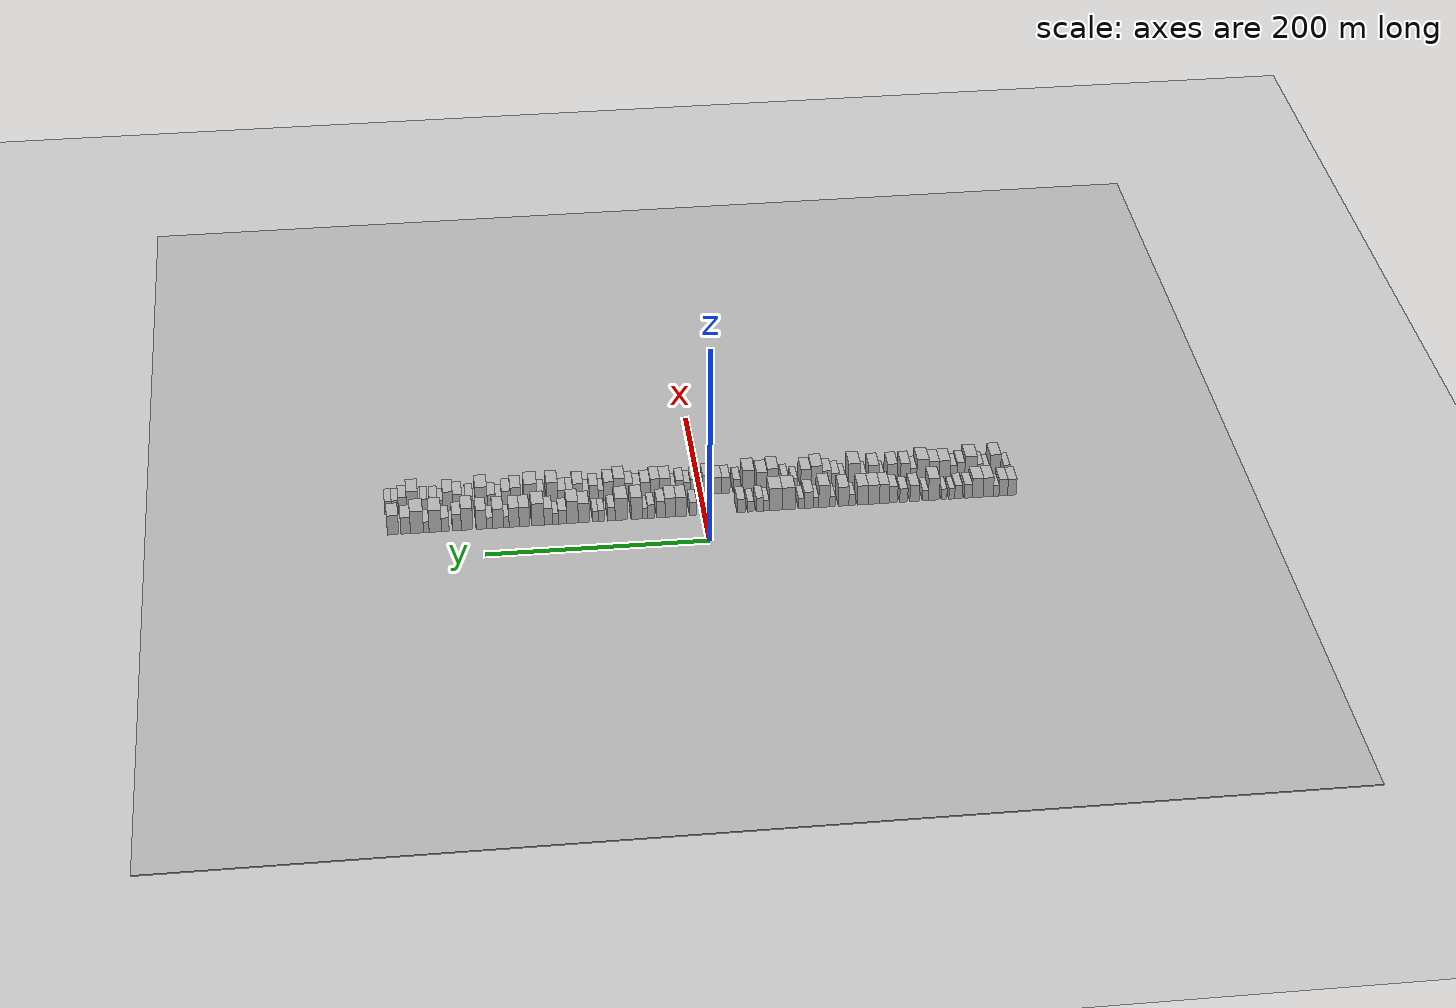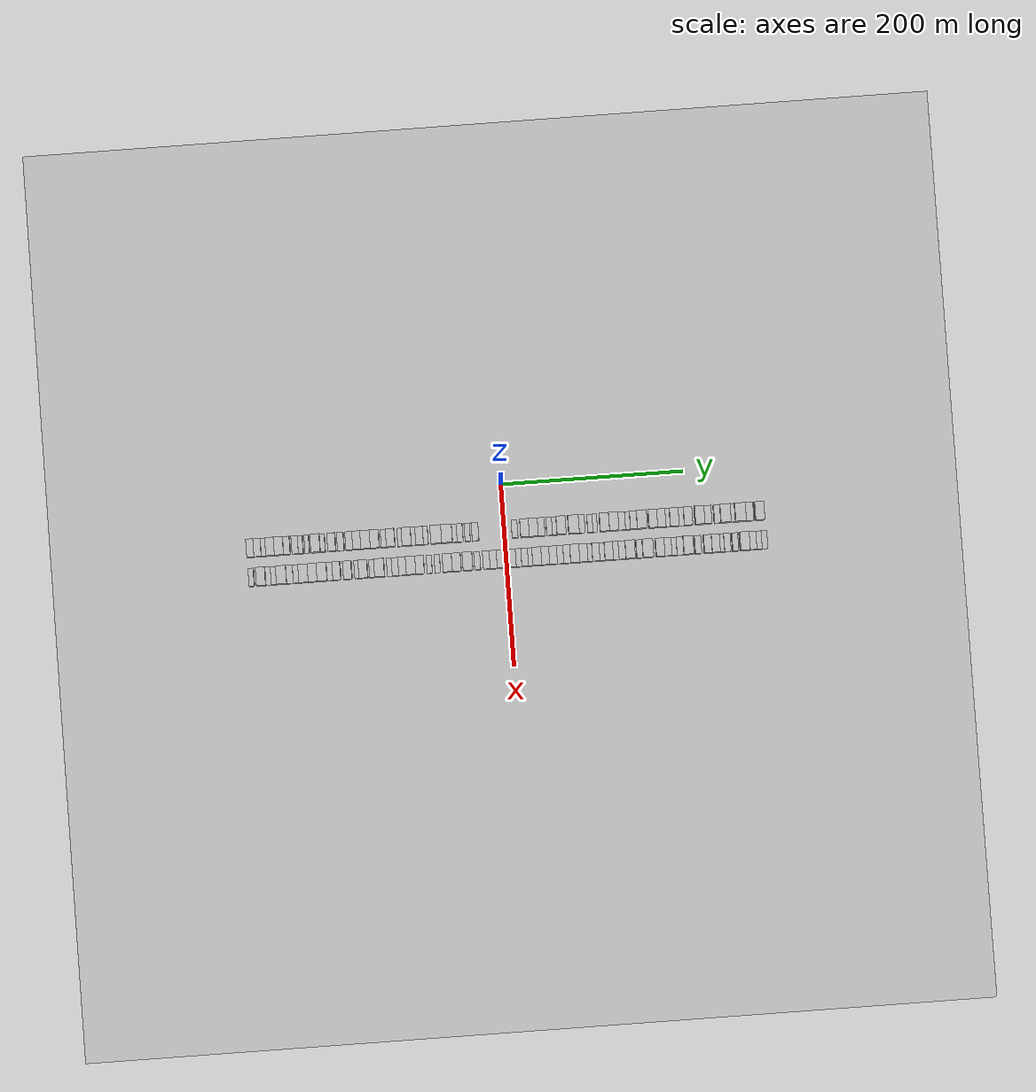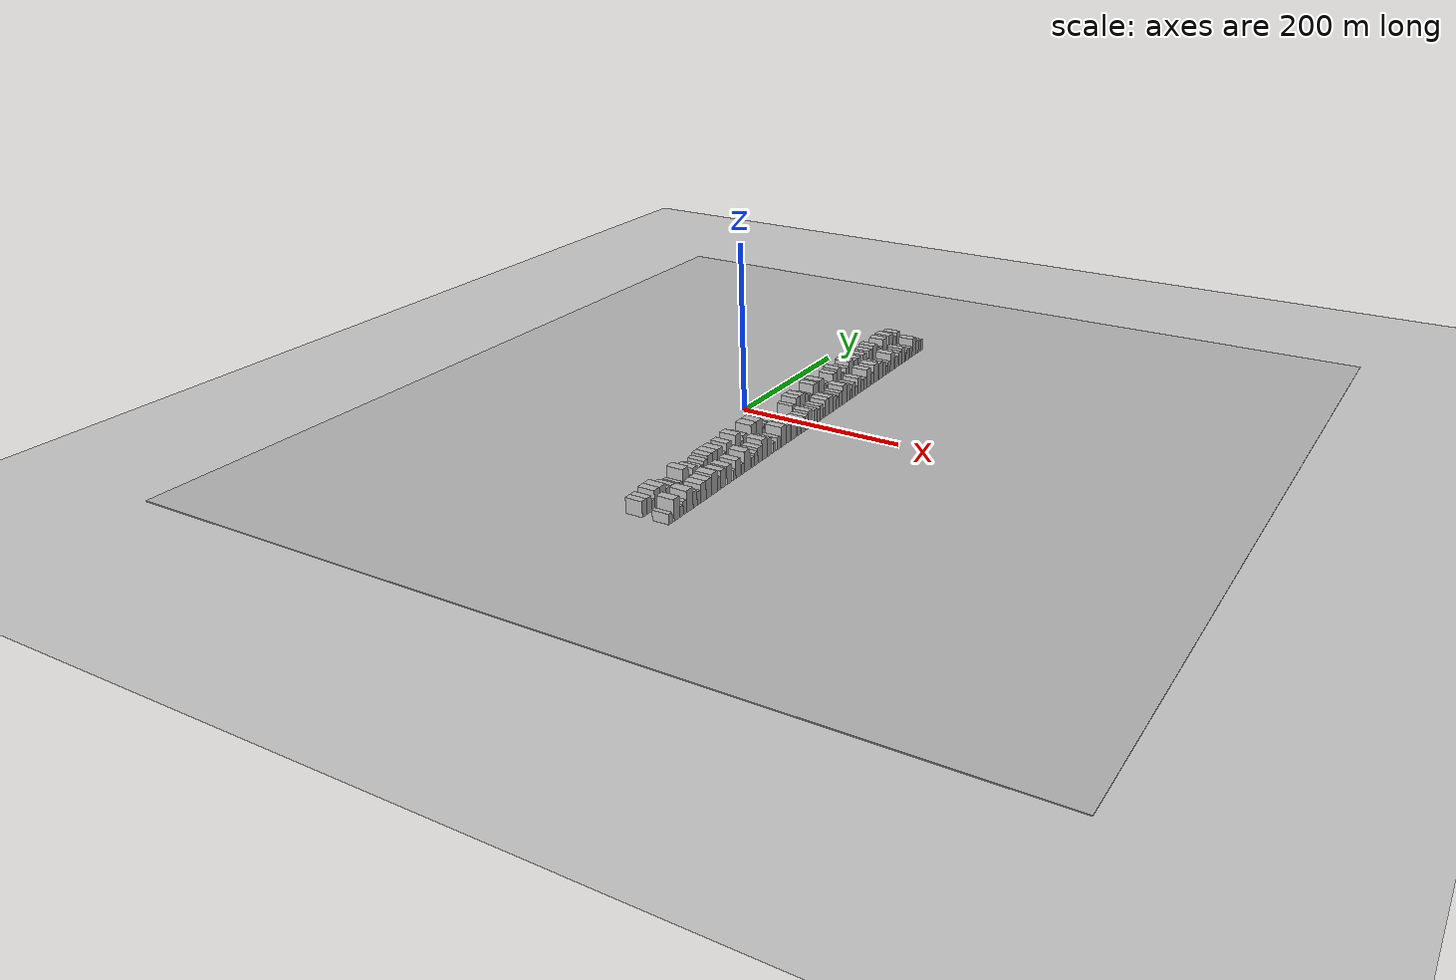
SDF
<?xml version="1.0" encoding="utf-8"?>

<sdf version="1.6">

   <world name="default">

      <gui fullscreen="0">

         <camera name="user_camera">

            <pose>-15 0 4.57585 0 0 0</pose>

            <view_controller>orbit</view_controller>

         </camera>

      </gui>

      <scene>

         <sky>

           <clouds>

             <speed>12</speed>

           </clouds>

         </sky>

         <ambient>0.4 0.4 0.4 1</ambient>

         <background>0.7 0.7 0.7 1</background>

         <shadows>1</shadows>

      </scene>

      <gravity>0 0 -9.8066</gravity>

      <magnetic_field>6e-06 2.3e-05 -4.2e-05</magnetic_field>

      <physics default="0" name="default_physics" type="ode">

         <ode>

            <solver>

               <type>quick</type>

               <iters>10</iters>

               <sor>1.0</sor>

               <use_dynamic_moi_rescaling>0</use_dynamic_moi_rescaling>

            </solver>

            <constraints>

               <cfm>0</cfm>

               <erp>0.2</erp>

               <contact_max_correcting_vel>100</contact_max_correcting_vel>

               <contact_surface_layer>0.001</contact_surface_layer>

            </constraints>

         </ode>

         <max_step_size>0.004</max_step_size>

         <real_time_factor>1</real_time_factor>

         <real_time_update_rate>250</real_time_update_rate>

      </physics>

      <light name="sun" type="directional">

         <cast_shadows>1</cast_shadows>

         <pose>0 0 10 0 0 0</pose>

         <diffuse>0.8 0.8 0.8 1</diffuse>

         <specular>0.2 0.2 0.2 1</specular>

         <attenuation>

            <range>1000</range>

            <constant>0.9</constant>

            <linear>0.01</linear>

            <quadratic>0.001</quadratic>

         </attenuation>

         <direction>-0.5 0.1 -0.9</direction>

      </light>

      <include>

         <name>ground_plane_1</name>

         <uri>model://HANNAS_ground_plane</uri>

         <pose>0 0 0  0 0 0</pose>

      </include>

      <include>

         <name>ground_plane_2</name>

         <uri>model://HANNAS_ground_plane</uri>

         <pose>100 0 0  0 0 0</pose>

      </include>

      <model name="building_1">

         <static>1</static>

         <pose frame="">50.0000 -280.0418 0 0.000000 0.000000 0.000000</pose>

         <link name="link">

            <pose frame="">0 0 9.00 0 0 0</pose>

            <collision name="collision">

               <geometry>

                  <box>

                     <size>20.0000 7.9164 18.0000</size>

                  </box>

               </geometry>

               <max_contacts>10</max_contacts>

               <surface>

                  <contact>

                     <ode/>

                  </contact>

                  <bounce/>

                  <friction>

                     <torsional>

                        <ode/>

                     </torsional>

                     <ode/>

                  </friction>

               </surface>

            </collision>

            <visual name="visual">

               <cast_shadows>0</cast_shadows>

               <geometry>

                  <box>

                     <size>20.0000 7.9164 18.0000</size>

                  </box>

               </geometry>

               <material>

                  <script>

                     <uri>model://HANNAS_wall/materials/scripts</uri>

                     <uri>model://HANNAS_wall/materials/textures</uri>

                     <name>vrc/HANNAS_wall</name>

                  </script>

               </material>

            </visual>

            <self_collide>0</self_collide>

            <enable_wind>0</enable_wind>

            <kinematic>0</kinematic>

         </link>

      </model>

      <model name="building_2">

         <static>1</static>

         <pose frame="">50.0000 -272.1381 0 0.000000 0.000000 0.000000</pose>

         <link name="link">

            <pose frame="">0 0 9.00 0 0 0</pose>

            <collision name="collision">

               <geometry>

                  <box>

                     <size>20.0000 7.8909 18.0000</size>

                  </box>

               </geometry>

               <max_contacts>10</max_contacts>

               <surface>

                  <contact>

                     <ode/>

                  </contact>

                  <bounce/>

                  <friction>

                     <torsional>

                        <ode/>

                     </torsional>

                     <ode/>

                  </friction>

               </surface>

            </collision>

            <visual name="visual">

               <cast_shadows>0</cast_shadows>

               <geometry>

                  <box>

                     <size>20.0000 7.8909 18.0000</size>

                  </box>

               </geometry>

               <material>

                  <script>

                     <uri>model://HANNAS_wall/materials/scripts</uri>

                     <uri>model://HANNAS_wall/materials/textures</uri>

                     <name>vrc/HANNAS_wall</name>

                  </script>

               </material>

            </visual>

            <self_collide>0</self_collide>

            <enable_wind>0</enable_wind>

            <kinematic>0</kinematic>

         </link>

      </model>

      <model name="building_3">

         <static>1</static>

         <pose frame="">50.0000 -265.5520 0 0.000000 0.000000 0.000000</pose>

         <link name="link">

            <pose frame="">0 0 6.00 0 0 0</pose>

            <collision name="collision">

               <geometry>

                  <box>

                     <size>20.0000 5.2812 12.0000</size>

                  </box>

               </geometry>

               <max_contacts>10</max_contacts>

               <surface>

                  <contact>

                     <ode/>

                  </contact>

                  <bounce/>

                  <friction>

                     <torsional>

                        <ode/>

                     </torsional>

                     <ode/>

                  </friction>

               </surface>

            </collision>

            <visual name="visual">

               <cast_shadows>0</cast_shadows>

               <geometry>

                  <box>

                     <size>20.0000 5.2812 12.0000</size>

                  </box>

               </geometry>

               <material>

                  <script>

                     <uri>model://HANNAS_wall/materials/scripts</uri>

                     <uri>model://HANNAS_wall/materials/textures</uri>

                     <name>vrc/HANNAS_wall</name>

                  </script>

               </material>

            </visual>

            <self_collide>0</self_collide>

            <enable_wind>0</enable_wind>

            <kinematic>0</kinematic>

         </link>

      </model>

      <model name="building_4">

         <static>1</static>

         <pose frame="">50.0000 -258.2314 0 0.000000 0.000000 0.000000</pose>

         <link name="link">

            <pose frame="">0 0 10.50 0 0 0</pose>

            <collision name="collision">

               <geometry>

                  <box>

                     <size>20.0000 9.3601 21.0000</size>

                  </box>

               </geometry>

               <max_contacts>10</max_contacts>

               <surface>

                  <contact>

                     <ode/>

                  </contact>

                  <bounce/>

                  <friction>

                     <torsional>

                        <ode/>

                     </torsional>

                     <ode/>

                  </friction>

               </surface>

            </collision>

            <visual name="visual">

               <cast_shadows>0</cast_shadows>

               <geometry>

                  <box>

                     <size>20.0000 9.3601 21.0000</size>

                  </box>

               </geometry>

               <material>

                  <script>

                     <uri>model://HANNAS_wall/materials/scripts</uri>

                     <uri>model://HANNAS_wall/materials/textures</uri>

                     <name>vrc/HANNAS_wall</name>

                  </script>

               </material>

            </visual>

            <self_collide>0</self_collide>

            <enable_wind>0</enable_wind>

            <kinematic>0</kinematic>

         </link>

      </model>

      <model name="building_5">

         <static>1</static>

         <pose frame="">50.0000 -248.5249 0 0.000000 0.000000 0.000000</pose>

         <link name="link">

            <pose frame="">0 0 10.50 0 0 0</pose>

            <collision name="collision">

               <geometry>

                  <box>

                     <size>20.0000 10.0527 21.0000</size>

                  </box>

               </geometry>

               <max_contacts>10</max_contacts>

               <surface>

                  <contact>

                     <ode/>

                  </contact>

                  <bounce/>

                  <friction>

                     <torsional>

                        <ode/>

                     </torsional>

                     <ode/>

                  </friction>

               </surface>

            </collision>

            <visual name="visual">

               <cast_shadows>0</cast_shadows>

               <geometry>

                  <box>

                     <size>20.0000 10.0527 21.0000</size>

                  </box>

               </geometry>

               <material>

                  <script>

                     <uri>model://HANNAS_wall/materials/scripts</uri>

                     <uri>model://HANNAS_wall/materials/textures</uri>

                     <name>vrc/HANNAS_wall</name>

                  </script>

               </material>

            </visual>

            <self_collide>0</self_collide>

            <enable_wind>0</enable_wind>

            <kinematic>0</kinematic>

         </link>

      </model>

      <model name="building_6">

         <static>1</static>

         <pose frame="">50.0000 -239.9425 0 0.000000 0.000000 0.000000</pose>

         <link name="link">

            <pose frame="">0 0 7.50 0 0 0</pose>

            <collision name="collision">

               <geometry>

                  <box>

                     <size>20.0000 7.1122 15.0000</size>

                  </box>

               </geometry>

               <max_contacts>10</max_contacts>

               <surface>

                  <contact>

                     <ode/>

                  </contact>

                  <bounce/>

                  <friction>

                     <torsional>

                        <ode/>

                     </torsional>

                     <ode/>

                  </friction>

               </surface>

            </collision>

            <visual name="visual">

               <cast_shadows>0</cast_shadows>

               <geometry>

                  <box>

                     <size>20.0000 7.1122 15.0000</size>

                  </box>

               </geometry>

               <material>

                  <script>

                     <uri>model://HANNAS_wall/materials/scripts</uri>

                     <uri>model://HANNAS_wall/materials/textures</uri>

                     <name>vrc/HANNAS_wall</name>

                  </script>

               </material>

            </visual>

            <self_collide>0</self_collide>

            <enable_wind>0</enable_wind>

            <kinematic>0</kinematic>

         </link>

      </model>

      <model name="building_7">

         <static>1</static>

         <pose frame="">50.0000 -230.9137 0 0.000000 0.000000 0.000000</pose>

         <link name="link">

            <pose frame="">0 0 7.50 0 0 0</pose>

            <collision name="collision">

               <geometry>

                  <box>

                     <size>20.0000 6.9454 15.0000</size>

                  </box>

               </geometry>

               <max_contacts>10</max_contacts>

               <surface>

                  <contact>

                     <ode/>

                  </contact>

                  <bounce/>

                  <friction>

                     <torsional>

                        <ode/>

                     </torsional>

                     <ode/>

                  </friction>

               </surface>

            </collision>

            <visual name="visual">

               <cast_shadows>0</cast_shadows>

               <geometry>

                  <box>

                     <size>20.0000 6.9454 15.0000</size>

                  </box>

               </geometry>

               <material>

                  <script>

                     <uri>model://HANNAS_wall/materials/scripts</uri>

                     <uri>model://HANNAS_wall/materials/textures</uri>

                     <name>vrc/HANNAS_wall</name>

                  </script>

               </material>

            </visual>

            <self_collide>0</self_collide>

            <enable_wind>0</enable_wind>

            <kinematic>0</kinematic>

         </link>

      </model>

      <model name="building_8">

         <static>1</static>

         <pose frame="">50.0000 -224.8101 0 0.000000 0.000000 0.000000</pose>

         <link name="link">

            <pose frame="">0 0 6.00 0 0 0</pose>

            <collision name="collision">

               <geometry>

                  <box>

                     <size>20.0000 5.2617 12.0000</size>

                  </box>

               </geometry>

               <max_contacts>10</max_contacts>

               <surface>

                  <contact>

                     <ode/>

                  </contact>

                  <bounce/>

                  <friction>

                     <torsional>

                        <ode/>

                     </torsional>

                     <ode/>

                  </friction>

               </surface>

            </collision>

            <visual name="visual">

               <cast_shadows>0</cast_shadows>

               <geometry>

                  <box>

                     <size>20.0000 5.2617 12.0000</size>

                  </box>

               </geometry>

               <material>

                  <script>

                     <uri>model://HANNAS_wall/materials/scripts</uri>

                     <uri>model://HANNAS_wall/materials/textures</uri>

                     <name>vrc/HANNAS_wall</name>

                  </script>

               </material>

            </visual>

            <self_collide>0</self_collide>

            <enable_wind>0</enable_wind>

            <kinematic>0</kinematic>

         </link>

      </model>

      <model name="building_9">

         <static>1</static>

         <pose frame="">50.0000 -217.7683 0 0.000000 0.000000 0.000000</pose>

         <link name="link">

            <pose frame="">0 0 6.00 0 0 0</pose>

            <collision name="collision">

               <geometry>

                  <box>

                     <size>20.0000 4.8219 12.0000</size>

                  </box>

               </geometry>

               <max_contacts>10</max_contacts>

               <surface>

                  <contact>

                     <ode/>

                  </contact>

                  <bounce/>

                  <friction>

                     <torsional>

                        <ode/>

                     </torsional>

                     <ode/>

                  </friction>

               </surface>

            </collision>

            <visual name="visual">

               <cast_shadows>0</cast_shadows>

               <geometry>

                  <box>

                     <size>20.0000 4.8219 12.0000</size>

                  </box>

               </geometry>

               <material>

                  <script>

                     <uri>model://HANNAS_wall/materials/scripts</uri>

                     <uri>model://HANNAS_wall/materials/textures</uri>

                     <name>vrc/HANNAS_wall</name>

                  </script>

               </material>

            </visual>

            <self_collide>0</self_collide>

            <enable_wind>0</enable_wind>

            <kinematic>0</kinematic>

         </link>

      </model>

      <model name="building_10">

         <static>1</static>

         <pose frame="">50.0000 -208.3083 0 0.000000 0.000000 0.000000</pose>

         <link name="link">

            <pose frame="">0 0 12.00 0 0 0</pose>

            <collision name="collision">

               <geometry>

                  <box>

                     <size>20.0000 10.0980 24.0000</size>

                  </box>

               </geometry>

               <max_contacts>10</max_contacts>

               <surface>

                  <contact>

                     <ode/>

                  </contact>

                  <bounce/>

                  <friction>

                     <torsional>

                        <ode/>

                     </torsional>

                     <ode/>

                  </friction>

               </surface>

            </collision>

            <visual name="visual">

               <cast_shadows>0</cast_shadows>

               <geometry>

                  <box>

                     <size>20.0000 10.0980 24.0000</size>

                  </box>

               </geometry>

               <material>

                  <script>

                     <uri>model://HANNAS_wall/materials/scripts</uri>

                     <uri>model://HANNAS_wall/materials/textures</uri>

                     <name>vrc/HANNAS_wall</name>

                  </script>

               </material>

            </visual>

            <self_collide>0</self_collide>

            <enable_wind>0</enable_wind>

            <kinematic>0</kinematic>

         </link>

      </model>

      <model name="building_11">

         <static>1</static>

         <pose frame="">50.0000 -200.6108 0 0.000000 0.000000 0.000000</pose>

         <link name="link">

            <pose frame="">0 0 6.00 0 0 0</pose>

            <collision name="collision">

               <geometry>

                  <box>

                     <size>20.0000 5.2971 12.0000</size>

                  </box>

               </geometry>

               <max_contacts>10</max_contacts>

               <surface>

                  <contact>

                     <ode/>

                  </contact>

                  <bounce/>

                  <friction>

                     <torsional>

                        <ode/>

                     </torsional>

                     <ode/>

                  </friction>

               </surface>

            </collision>

            <visual name="visual">

               <cast_shadows>0</cast_shadows>

               <geometry>

                  <box>

                     <size>20.0000 5.2971 12.0000</size>

                  </box>

               </geometry>

               <material>

                  <script>

                     <uri>model://HANNAS_wall/materials/scripts</uri>

                     <uri>model://HANNAS_wall/materials/textures</uri>

                     <name>vrc/HANNAS_wall</name>

                  </script>

               </material>

            </visual>

            <self_collide>0</self_collide>

            <enable_wind>0</enable_wind>

            <kinematic>0</kinematic>

         </link>

      </model>

      <model name="building_12">

         <static>1</static>

         <pose frame="">50.0000 -190.6578 0 0.000000 0.000000 0.000000</pose>

         <link name="link">

            <pose frame="">0 0 9.00 0 0 0</pose>

            <collision name="collision">

               <geometry>

                  <box>

                     <size>20.0000 8.6088 18.0000</size>

                  </box>

               </geometry>

               <max_contacts>10</max_contacts>

               <surface>

                  <contact>

                     <ode/>

                  </contact>

                  <bounce/>

                  <friction>

                     <torsional>

                        <ode/>

                     </torsional>

                     <ode/>

                  </friction>

               </surface>

            </collision>

            <visual name="visual">

               <cast_shadows>0</cast_shadows>

               <geometry>

                  <box>

                     <size>20.0000 8.6088 18.0000</size>

                  </box>

               </geometry>

               <material>

                  <script>

                     <uri>model://HANNAS_wall/materials/scripts</uri>

                     <uri>model://HANNAS_wall/materials/textures</uri>

                     <name>vrc/HANNAS_wall</name>

                  </script>

               </material>

            </visual>

            <self_collide>0</self_collide>

            <enable_wind>0</enable_wind>

            <kinematic>0</kinematic>

         </link>

      </model>

      <model name="building_13">

         <static>1</static>

         <pose frame="">50.0000 -180.7270 0 0.000000 0.000000 0.000000</pose>

         <link name="link">

            <pose frame="">0 0 7.50 0 0 0</pose>

            <collision name="collision">

               <geometry>

                  <box>

                     <size>20.0000 7.2529 15.0000</size>

                  </box>

               </geometry>

               <max_contacts>10</max_contacts>

               <surface>

                  <contact>

                     <ode/>

                  </contact>

                  <bounce/>

                  <friction>

                     <torsional>

                        <ode/>

                     </torsional>

                     <ode/>

                  </friction>

               </surface>

            </collision>

            <visual name="visual">

               <cast_shadows>0</cast_shadows>

               <geometry>

                  <box>

                     <size>20.0000 7.2529 15.0000</size>

                  </box>

               </geometry>

               <material>

                  <script>

                     <uri>model://HANNAS_wall/materials/scripts</uri>

                     <uri>model://HANNAS_wall/materials/textures</uri>

                     <name>vrc/HANNAS_wall</name>

                  </script>

               </material>

            </visual>

            <self_collide>0</self_collide>

            <enable_wind>0</enable_wind>

            <kinematic>0</kinematic>

         </link>

      </model>

      <model name="building_14">

         <static>1</static>

         <pose frame="">50.0000 -171.2590 0 0.000000 0.000000 0.000000</pose>

         <link name="link">

            <pose frame="">0 0 9.00 0 0 0</pose>

            <collision name="collision">

               <geometry>

                  <box>

                     <size>20.0000 7.6830 18.0000</size>

                  </box>

               </geometry>

               <max_contacts>10</max_contacts>

               <surface>

                  <contact>

                     <ode/>

                  </contact>

                  <bounce/>

                  <friction>

                     <torsional>

                        <ode/>

                     </torsional>

                     <ode/>

                  </friction>

               </surface>

            </collision>

            <visual name="visual">

               <cast_shadows>0</cast_shadows>

               <geometry>

                  <box>

                     <size>20.0000 7.6830 18.0000</size>

                  </box>

               </geometry>

               <material>

                  <script>

                     <uri>model://HANNAS_wall/materials/scripts</uri>

                     <uri>model://HANNAS_wall/materials/textures</uri>

                     <name>vrc/HANNAS_wall</name>

                  </script>

               </material>

            </visual>

            <self_collide>0</self_collide>

            <enable_wind>0</enable_wind>

            <kinematic>0</kinematic>

         </link>

      </model>

      <model name="building_15">

         <static>1</static>

         <pose frame="">50.0000 -162.9689 0 0.000000 0.000000 0.000000</pose>

         <link name="link">

            <pose frame="">0 0 10.50 0 0 0</pose>

            <collision name="collision">

               <geometry>

                  <box>

                     <size>20.0000 8.8972 21.0000</size>

                  </box>

               </geometry>

               <max_contacts>10</max_contacts>

               <surface>

                  <contact>

                     <ode/>

                  </contact>

                  <bounce/>

                  <friction>

                     <torsional>

                        <ode/>

                     </torsional>

                     <ode/>

                  </friction>

               </surface>

            </collision>

            <visual name="visual">

               <cast_shadows>0</cast_shadows>

               <geometry>

                  <box>

                     <size>20.0000 8.8972 21.0000</size>

                  </box>

               </geometry>

               <material>

                  <script>

                     <uri>model://HANNAS_wall/materials/scripts</uri>

                     <uri>model://HANNAS_wall/materials/textures</uri>

                     <name>vrc/HANNAS_wall</name>

                  </script>

               </material>

            </visual>

            <self_collide>0</self_collide>

            <enable_wind>0</enable_wind>

            <kinematic>0</kinematic>

         </link>

      </model>

      <model name="building_16">

         <static>1</static>

         <pose frame="">50.0000 -153.3643 0 0.000000 0.000000 0.000000</pose>

         <link name="link">

            <pose frame="">0 0 10.50 0 0 0</pose>

            <collision name="collision">

               <geometry>

                  <box>

                     <size>20.0000 10.3121 21.0000</size>

                  </box>

               </geometry>

               <max_contacts>10</max_contacts>

               <surface>

                  <contact>

                     <ode/>

                  </contact>

                  <bounce/>

                  <friction>

                     <torsional>

                        <ode/>

                     </torsional>

                     <ode/>

                  </friction>

               </surface>

            </collision>

            <visual name="visual">

               <cast_shadows>0</cast_shadows>

               <geometry>

                  <box>

                     <size>20.0000 10.3121 21.0000</size>

                  </box>

               </geometry>

               <material>

                  <script>

                     <uri>model://HANNAS_wall/materials/scripts</uri>

                     <uri>model://HANNAS_wall/materials/textures</uri>

                     <name>vrc/HANNAS_wall</name>

                  </script>

               </material>

            </visual>

            <self_collide>0</self_collide>

            <enable_wind>0</enable_wind>

            <kinematic>0</kinematic>

         </link>

      </model>

      <model name="building_17">

         <static>1</static>

         <pose frame="">50.0000 -143.2969 0 0.000000 0.000000 0.000000</pose>

         <link name="link">

            <pose frame="">0 0 10.50 0 0 0</pose>

            <collision name="collision">

               <geometry>

                  <box>

                     <size>20.0000 9.8226 21.0000</size>

                  </box>

               </geometry>

               <max_contacts>10</max_contacts>

               <surface>

                  <contact>

                     <ode/>

                  </contact>

                  <bounce/>

                  <friction>

                     <torsional>

                        <ode/>

                     </torsional>

                     <ode/>

                  </friction>

               </surface>

            </collision>

            <visual name="visual">

               <cast_shadows>0</cast_shadows>

               <geometry>

                  <box>

                     <size>20.0000 9.8226 21.0000</size>

                  </box>

               </geometry>

               <material>

                  <script>

                     <uri>model://HANNAS_wall/materials/scripts</uri>

                     <uri>model://HANNAS_wall/materials/textures</uri>

                     <name>vrc/HANNAS_wall</name>

                  </script>

               </material>

            </visual>

            <self_collide>0</self_collide>

            <enable_wind>0</enable_wind>

            <kinematic>0</kinematic>

         </link>

      </model>

      <model name="building_18">

         <static>1</static>

         <pose frame="">50.0000 -133.5060 0 0.000000 0.000000 0.000000</pose>

         <link name="link">

            <pose frame="">0 0 6.00 0 0 0</pose>

            <collision name="collision">

               <geometry>

                  <box>

                     <size>20.0000 5.7592 12.0000</size>

                  </box>

               </geometry>

               <max_contacts>10</max_contacts>

               <surface>

                  <contact>

                     <ode/>

                  </contact>

                  <bounce/>

                  <friction>

                     <torsional>

                        <ode/>

                     </torsional>

                     <ode/>

                  </friction>

               </surface>

            </collision>

            <visual name="visual">

               <cast_shadows>0</cast_shadows>

               <geometry>

                  <box>

                     <size>20.0000 5.7592 12.0000</size>

                  </box>

               </geometry>

               <material>

                  <script>

                     <uri>model://HANNAS_wall/materials/scripts</uri>

                     <uri>model://HANNAS_wall/materials/textures</uri>

                     <name>vrc/HANNAS_wall</name>

                  </script>

               </material>

            </visual>

            <self_collide>0</self_collide>

            <enable_wind>0</enable_wind>

            <kinematic>0</kinematic>

         </link>

      </model>

      <model name="building_19">

         <static>1</static>

         <pose frame="">50.0000 -125.8927 0 0.000000 0.000000 0.000000</pose>

         <link name="link">

            <pose frame="">0 0 10.50 0 0 0</pose>

            <collision name="collision">

               <geometry>

                  <box>

                     <size>20.0000 9.4675 21.0000</size>

                  </box>

               </geometry>

               <max_contacts>10</max_contacts>

               <surface>

                  <contact>

                     <ode/>

                  </contact>

                  <bounce/>

                  <friction>

                     <torsional>

                        <ode/>

                     </torsional>

                     <ode/>

                  </friction>

               </surface>

            </collision>

            <visual name="visual">

               <cast_shadows>0</cast_shadows>

               <geometry>

                  <box>

                     <size>20.0000 9.4675 21.0000</size>

                  </box>

               </geometry>

               <material>

                  <script>

                     <uri>model://HANNAS_wall/materials/scripts</uri>

                     <uri>model://HANNAS_wall/materials/textures</uri>

                     <name>vrc/HANNAS_wall</name>

                  </script>

               </material>

            </visual>

            <self_collide>0</self_collide>

            <enable_wind>0</enable_wind>

            <kinematic>0</kinematic>

         </link>

      </model>

      <model name="building_20">

         <static>1</static>

         <pose frame="">50.0000 -115.6931 0 0.000000 0.000000 0.000000</pose>

         <link name="link">

            <pose frame="">0 0 6.00 0 0 0</pose>

            <collision name="collision">

               <geometry>

                  <box>

                     <size>20.0000 4.9316 12.0000</size>

                  </box>

               </geometry>

               <max_contacts>10</max_contacts>

               <surface>

                  <contact>

                     <ode/>

                  </contact>

                  <bounce/>

                  <friction>

                     <torsional>

                        <ode/>

                     </torsional>

                     <ode/>

                  </friction>

               </surface>

            </collision>

            <visual name="visual">

               <cast_shadows>0</cast_shadows>

               <geometry>

                  <box>

                     <size>20.0000 4.9316 12.0000</size>

                  </box>

               </geometry>

               <material>

                  <script>

                     <uri>model://HANNAS_wall/materials/scripts</uri>

                     <uri>model://HANNAS_wall/materials/textures</uri>

                     <name>vrc/HANNAS_wall</name>

                  </script>

               </material>

            </visual>

            <self_collide>0</self_collide>

            <enable_wind>0</enable_wind>

            <kinematic>0</kinematic>

         </link>

      </model>

      <model name="building_21">

         <static>1</static>

         <pose frame="">50.0000 -108.1800 0 0.000000 0.000000 0.000000</pose>

         <link name="link">

            <pose frame="">0 0 12.00 0 0 0</pose>

            <collision name="collision">

               <geometry>

                  <box>

                     <size>20.0000 10.0948 24.0000</size>

                  </box>

               </geometry>

               <max_contacts>10</max_contacts>

               <surface>

                  <contact>

                     <ode/>

                  </contact>

                  <bounce/>

                  <friction>

                     <torsional>

                        <ode/>

                     </torsional>

                     <ode/>

                  </friction>

               </surface>

            </collision>

            <visual name="visual">

               <cast_shadows>0</cast_shadows>

               <geometry>

                  <box>

                     <size>20.0000 10.0948 24.0000</size>

                  </box>

               </geometry>

               <material>

                  <script>

                     <uri>model://HANNAS_wall/materials/scripts</uri>

                     <uri>model://HANNAS_wall/materials/textures</uri>

                     <name>vrc/HANNAS_wall</name>

                  </script>

               </material>

            </visual>

            <self_collide>0</self_collide>

            <enable_wind>0</enable_wind>

            <kinematic>0</kinematic>

         </link>

      </model>

      <model name="building_22">

         <static>1</static>

         <pose frame="">50.0000 -100.7014 0 0.000000 0.000000 0.000000</pose>

         <link name="link">

            <pose frame="">0 0 6.00 0 0 0</pose>

            <collision name="collision">

               <geometry>

                  <box>

                     <size>20.0000 4.8624 12.0000</size>

                  </box>

               </geometry>

               <max_contacts>10</max_contacts>

               <surface>

                  <contact>

                     <ode/>

                  </contact>

                  <bounce/>

                  <friction>

                     <torsional>

                        <ode/>

                     </torsional>

                     <ode/>

                  </friction>

               </surface>

            </collision>

            <visual name="visual">

               <cast_shadows>0</cast_shadows>

               <geometry>

                  <box>

                     <size>20.0000 4.8624 12.0000</size>

                  </box>

               </geometry>

               <material>

                  <script>

                     <uri>model://HANNAS_wall/materials/scripts</uri>

                     <uri>model://HANNAS_wall/materials/textures</uri>

                     <name>vrc/HANNAS_wall</name>

                  </script>

               </material>

            </visual>

            <self_collide>0</self_collide>

            <enable_wind>0</enable_wind>

            <kinematic>0</kinematic>

         </link>

      </model>

      <model name="building_23">

         <static>1</static>

         <pose frame="">50.0000 -94.0933 0 0.000000 0.000000 0.000000</pose>

         <link name="link">

            <pose frame="">0 0 9.00 0 0 0</pose>

            <collision name="collision">

               <geometry>

                  <box>

                     <size>20.0000 8.3538 18.0000</size>

                  </box>

               </geometry>

               <max_contacts>10</max_contacts>

               <surface>

                  <contact>

                     <ode/>

                  </contact>

                  <bounce/>

                  <friction>

                     <torsional>

                        <ode/>

                     </torsional>

                     <ode/>

                  </friction>

               </surface>

            </collision>

            <visual name="visual">

               <cast_shadows>0</cast_shadows>

               <geometry>

                  <box>

                     <size>20.0000 8.3538 18.0000</size>

                  </box>

               </geometry>

               <material>

                  <script>

                     <uri>model://HANNAS_wall/materials/scripts</uri>

                     <uri>model://HANNAS_wall/materials/textures</uri>

                     <name>vrc/HANNAS_wall</name>

                  </script>

               </material>

            </visual>

            <self_collide>0</self_collide>

            <enable_wind>0</enable_wind>

            <kinematic>0</kinematic>

         </link>

      </model>

      <model name="building_24">

         <static>1</static>

         <pose frame="">50.0000 -87.2946 0 0.000000 0.000000 0.000000</pose>

         <link name="link">

            <pose frame="">0 0 6.00 0 0 0</pose>

            <collision name="collision">

               <geometry>

                  <box>

                     <size>20.0000 5.2435 12.0000</size>

                  </box>

               </geometry>

               <max_contacts>10</max_contacts>

               <surface>

                  <contact>

                     <ode/>

                  </contact>

                  <bounce/>

                  <friction>

                     <torsional>

                        <ode/>

                     </torsional>

                     <ode/>

                  </friction>

               </surface>

            </collision>

            <visual name="visual">

               <cast_shadows>0</cast_shadows>

               <geometry>

                  <box>

                     <size>20.0000 5.2435 12.0000</size>

                  </box>

               </geometry>

               <material>

                  <script>

                     <uri>model://HANNAS_wall/materials/scripts</uri>

                     <uri>model://HANNAS_wall/materials/textures</uri>

                     <name>vrc/HANNAS_wall</name>

                  </script>

               </material>

            </visual>

            <self_collide>0</self_collide>

            <enable_wind>0</enable_wind>

            <kinematic>0</kinematic>

         </link>

      </model>

      <model name="building_25">

         <static>1</static>

         <pose frame="">50.0000 -75.7288 0 0.000000 0.000000 0.000000</pose>

         <link name="link">

            <pose frame="">0 0 12.00 0 0 0</pose>

            <collision name="collision">

               <geometry>

                  <box>

                     <size>20.0000 11.8882 24.0000</size>

                  </box>

               </geometry>

               <max_contacts>10</max_contacts>

               <surface>

                  <contact>

                     <ode/>

                  </contact>

                  <bounce/>

                  <friction>

                     <torsional>

                        <ode/>

                     </torsional>

                     <ode/>

                  </friction>

               </surface>

            </collision>

            <visual name="visual">

               <cast_shadows>0</cast_shadows>

               <geometry>

                  <box>

                     <size>20.0000 11.8882 24.0000</size>

                  </box>

               </geometry>

               <material>

                  <script>

                     <uri>model://HANNAS_wall/materials/scripts</uri>

                     <uri>model://HANNAS_wall/materials/textures</uri>

                     <name>vrc/HANNAS_wall</name>

                  </script>

               </material>

            </visual>

            <self_collide>0</self_collide>

            <enable_wind>0</enable_wind>

            <kinematic>0</kinematic>

         </link>

      </model>

      <model name="building_26">

         <static>1</static>

         <pose frame="">50.0000 -63.8923 0 0.000000 0.000000 0.000000</pose>

         <link name="link">

            <pose frame="">0 0 12.00 0 0 0</pose>

            <collision name="collision">

               <geometry>

                  <box>

                     <size>20.0000 11.7849 24.0000</size>

                  </box>

               </geometry>

               <max_contacts>10</max_contacts>

               <surface>

                  <contact>

                     <ode/>

                  </contact>

                  <bounce/>

                  <friction>

                     <torsional>

                        <ode/>

                     </torsional>

                     <ode/>

                  </friction>

               </surface>

            </collision>

            <visual name="visual">

               <cast_shadows>0</cast_shadows>

               <geometry>

                  <box>

                     <size>20.0000 11.7849 24.0000</size>

                  </box>

               </geometry>

               <material>

                  <script>

                     <uri>model://HANNAS_wall/materials/scripts</uri>

                     <uri>model://HANNAS_wall/materials/textures</uri>

                     <name>vrc/HANNAS_wall</name>

                  </script>

               </material>

            </visual>

            <self_collide>0</self_collide>

            <enable_wind>0</enable_wind>

            <kinematic>0</kinematic>

         </link>

      </model>

      <model name="building_27">

         <static>1</static>

         <pose frame="">50.0000 -55.4154 0 0.000000 0.000000 0.000000</pose>

         <link name="link">

            <pose frame="">0 0 6.00 0 0 0</pose>

            <collision name="collision">

               <geometry>

                  <box>

                     <size>20.0000 5.1688 12.0000</size>

                  </box>

               </geometry>

               <max_contacts>10</max_contacts>

               <surface>

                  <contact>

                     <ode/>

                  </contact>

                  <bounce/>

                  <friction>

                     <torsional>

                        <ode/>

                     </torsional>

                     <ode/>

                  </friction>

               </surface>

            </collision>

            <visual name="visual">

               <cast_shadows>0</cast_shadows>

               <geometry>

                  <box>

                     <size>20.0000 5.1688 12.0000</size>

                  </box>

               </geometry>

               <material>

                  <script>

                     <uri>model://HANNAS_wall/materials/scripts</uri>

                     <uri>model://HANNAS_wall/materials/textures</uri>

                     <name>vrc/HANNAS_wall</name>

                  </script>

               </material>

            </visual>

            <self_collide>0</self_collide>

            <enable_wind>0</enable_wind>

            <kinematic>0</kinematic>

         </link>

      </model>

      <model name="building_28">

         <static>1</static>

         <pose frame="">50.0000 -49.5430 0 0.000000 0.000000 0.000000</pose>

         <link name="link">

            <pose frame="">0 0 7.50 0 0 0</pose>

            <collision name="collision">

               <geometry>

                  <box>

                     <size>20.0000 6.5759 15.0000</size>

                  </box>

               </geometry>

               <max_contacts>10</max_contacts>

               <surface>

                  <contact>

                     <ode/>

                  </contact>

                  <bounce/>

                  <friction>

                     <torsional>

                        <ode/>

                     </torsional>

                     <ode/>

                  </friction>

               </surface>

            </collision>

            <visual name="visual">

               <cast_shadows>0</cast_shadows>

               <geometry>

                  <box>

                     <size>20.0000 6.5759 15.0000</size>

                  </box>

               </geometry>

               <material>

                  <script>

                     <uri>model://HANNAS_wall/materials/scripts</uri>

                     <uri>model://HANNAS_wall/materials/textures</uri>

                     <name>vrc/HANNAS_wall</name>

                  </script>

               </material>

            </visual>

            <self_collide>0</self_collide>

            <enable_wind>0</enable_wind>

            <kinematic>0</kinematic>

         </link>

      </model>

      <model name="building_29">

         <static>1</static>

         <pose frame="">50.0000 -41.3061 0 0.000000 0.000000 0.000000</pose>

         <link name="link">

            <pose frame="">0 0 6.00 0 0 0</pose>

            <collision name="collision">

               <geometry>

                  <box>

                     <size>20.0000 5.8980 12.0000</size>

                  </box>

               </geometry>

               <max_contacts>10</max_contacts>

               <surface>

                  <contact>

                     <ode/>

                  </contact>

                  <bounce/>

                  <friction>

                     <torsional>

                        <ode/>

                     </torsional>

                     <ode/>

                  </friction>

               </surface>

            </collision>

            <visual name="visual">

               <cast_shadows>0</cast_shadows>

               <geometry>

                  <box>

                     <size>20.0000 5.8980 12.0000</size>

                  </box>

               </geometry>

               <material>

                  <script>

                     <uri>model://HANNAS_wall/materials/scripts</uri>

                     <uri>model://HANNAS_wall/materials/textures</uri>

                     <name>vrc/HANNAS_wall</name>

                  </script>

               </material>

            </visual>

            <self_collide>0</self_collide>

            <enable_wind>0</enable_wind>

            <kinematic>0</kinematic>

         </link>

      </model>

      <model name="building_30">

         <static>1</static>

         <pose frame="">50.0000 -32.6399 0 0.000000 0.000000 0.000000</pose>

         <link name="link">

            <pose frame="">0 0 7.50 0 0 0</pose>

            <collision name="collision">

               <geometry>

                  <box>

                     <size>20.0000 7.4343 15.0000</size>

                  </box>

               </geometry>

               <max_contacts>10</max_contacts>

               <surface>

                  <contact>

                     <ode/>

                  </contact>

                  <bounce/>

                  <friction>

                     <torsional>

                        <ode/>

                     </torsional>

                     <ode/>

                  </friction>

               </surface>

            </collision>

            <visual name="visual">

               <cast_shadows>0</cast_shadows>

               <geometry>

                  <box>

                     <size>20.0000 7.4343 15.0000</size>

                  </box>

               </geometry>

               <material>

                  <script>

                     <uri>model://HANNAS_wall/materials/scripts</uri>

                     <uri>model://HANNAS_wall/materials/textures</uri>

                     <name>vrc/HANNAS_wall</name>

                  </script>

               </material>

            </visual>

            <self_collide>0</self_collide>

            <enable_wind>0</enable_wind>

            <kinematic>0</kinematic>

         </link>

      </model>

      <model name="building_31">

         <static>1</static>

         <pose frame="">50.0000 10.7931 0 0.000000 0.000000 0.000000</pose>

         <link name="link">

            <pose frame="">0 0 7.50 0 0 0</pose>

            <collision name="collision">

               <geometry>

                  <box>

                     <size>20.0000 6.4772 15.0000</size>

                  </box>

               </geometry>

               <max_contacts>10</max_contacts>

               <surface>

                  <contact>

                     <ode/>

                  </contact>

                  <bounce/>

                  <friction>

                     <torsional>

                        <ode/>

                     </torsional>

                     <ode/>

                  </friction>

               </surface>

            </collision>

            <visual name="visual">

               <cast_shadows>0</cast_shadows>

               <geometry>

                  <box>

                     <size>20.0000 6.4772 15.0000</size>

                  </box>

               </geometry>

               <material>

                  <script>

                     <uri>model://HANNAS_wall/materials/scripts</uri>

                     <uri>model://HANNAS_wall/materials/textures</uri>

                     <name>vrc/HANNAS_wall</name>

                  </script>

               </material>

            </visual>

            <self_collide>0</self_collide>

            <enable_wind>0</enable_wind>

            <kinematic>0</kinematic>

         </link>

      </model>

      <model name="building_32">

         <static>1</static>

         <pose frame="">50.0000 21.7320 0 0.000000 0.000000 0.000000</pose>

         <link name="link">

            <pose frame="">0 0 10.50 0 0 0</pose>

            <collision name="collision">

               <geometry>

                  <box>

                     <size>20.0000 9.4007 21.0000</size>

                  </box>

               </geometry>

               <max_contacts>10</max_contacts>

               <surface>

                  <contact>

                     <ode/>

                  </contact>

                  <bounce/>

                  <friction>

                     <torsional>

                        <ode/>

                     </torsional>

                     <ode/>

                  </friction>

               </surface>

            </collision>

            <visual name="visual">

               <cast_shadows>0</cast_shadows>

               <geometry>

                  <box>

                     <size>20.0000 9.4007 21.0000</size>

                  </box>

               </geometry>

               <material>

                  <script>

                     <uri>model://HANNAS_wall/materials/scripts</uri>

                     <uri>model://HANNAS_wall/materials/textures</uri>

                     <name>vrc/HANNAS_wall</name>

                  </script>

               </material>

            </visual>

            <self_collide>0</self_collide>

            <enable_wind>0</enable_wind>

            <kinematic>0</kinematic>

         </link>

      </model>

      <model name="building_33">

         <static>1</static>

         <pose frame="">50.0000 31.3498 0 0.000000 0.000000 0.000000</pose>

         <link name="link">

            <pose frame="">0 0 10.50 0 0 0</pose>

            <collision name="collision">

               <geometry>

                  <box>

                     <size>20.0000 9.8350 21.0000</size>

                  </box>

               </geometry>

               <max_contacts>10</max_contacts>

               <surface>

                  <contact>

                     <ode/>

                  </contact>

                  <bounce/>

                  <friction>

                     <torsional>

                        <ode/>

                     </torsional>

                     <ode/>

                  </friction>

               </surface>

            </collision>

            <visual name="visual">

               <cast_shadows>0</cast_shadows>

               <geometry>

                  <box>

                     <size>20.0000 9.8350 21.0000</size>

                  </box>

               </geometry>

               <material>

                  <script>

                     <uri>model://HANNAS_wall/materials/scripts</uri>

                     <uri>model://HANNAS_wall/materials/textures</uri>

                     <name>vrc/HANNAS_wall</name>

                  </script>

               </material>

            </visual>

            <self_collide>0</self_collide>

            <enable_wind>0</enable_wind>

            <kinematic>0</kinematic>

         </link>

      </model>

      <model name="building_34">

         <static>1</static>

         <pose frame="">50.0000 39.9967 0 0.000000 0.000000 0.000000</pose>

         <link name="link">

            <pose frame="">0 0 9.00 0 0 0</pose>

            <collision name="collision">

               <geometry>

                  <box>

                     <size>20.0000 7.4589 18.0000</size>

                  </box>

               </geometry>

               <max_contacts>10</max_contacts>

               <surface>

                  <contact>

                     <ode/>

                  </contact>

                  <bounce/>

                  <friction>

                     <torsional>

                        <ode/>

                     </torsional>

                     <ode/>

                  </friction>

               </surface>

            </collision>

            <visual name="visual">

               <cast_shadows>0</cast_shadows>

               <geometry>

                  <box>

                     <size>20.0000 7.4589 18.0000</size>

                  </box>

               </geometry>

               <material>

                  <script>

                     <uri>model://HANNAS_wall/materials/scripts</uri>

                     <uri>model://HANNAS_wall/materials/textures</uri>

                     <name>vrc/HANNAS_wall</name>

                  </script>

               </material>

            </visual>

            <self_collide>0</self_collide>

            <enable_wind>0</enable_wind>

            <kinematic>0</kinematic>

         </link>

      </model>

      <model name="building_35">

         <static>1</static>

         <pose frame="">50.0000 48.8616 0 0.000000 0.000000 0.000000</pose>

         <link name="link">

            <pose frame="">0 0 7.50 0 0 0</pose>

            <collision name="collision">

               <geometry>

                  <box>

                     <size>20.0000 6.2709 15.0000</size>

                  </box>

               </geometry>

               <max_contacts>10</max_contacts>

               <surface>

                  <contact>

                     <ode/>

                  </contact>

                  <bounce/>

                  <friction>

                     <torsional>

                        <ode/>

                     </torsional>

                     <ode/>

                  </friction>

               </surface>

            </collision>

            <visual name="visual">

               <cast_shadows>0</cast_shadows>

               <geometry>

                  <box>

                     <size>20.0000 6.2709 15.0000</size>

                  </box>

               </geometry>

               <material>

                  <script>

                     <uri>model://HANNAS_wall/materials/scripts</uri>

                     <uri>model://HANNAS_wall/materials/textures</uri>

                     <name>vrc/HANNAS_wall</name>

                  </script>

               </material>

            </visual>

            <self_collide>0</self_collide>

            <enable_wind>0</enable_wind>

            <kinematic>0</kinematic>

         </link>

      </model>

      <model name="building_36">

         <static>1</static>

         <pose frame="">50.0000 54.4242 0 0.000000 0.000000 0.000000</pose>

         <link name="link">

            <pose frame="">0 0 6.00 0 0 0</pose>

            <collision name="collision">

               <geometry>

                  <box>

                     <size>20.0000 4.8543 12.0000</size>

                  </box>

               </geometry>

               <max_contacts>10</max_contacts>

               <surface>

                  <contact>

                     <ode/>

                  </contact>

                  <bounce/>

                  <friction>

                     <torsional>

                        <ode/>

                     </torsional>

                     <ode/>

                  </friction>

               </surface>

            </collision>

            <visual name="visual">

               <cast_shadows>0</cast_shadows>

               <geometry>

                  <box>

                     <size>20.0000 4.8543 12.0000</size>

                  </box>

               </geometry>

               <material>

                  <script>

                     <uri>model://HANNAS_wall/materials/scripts</uri>

                     <uri>model://HANNAS_wall/materials/textures</uri>

                     <name>vrc/HANNAS_wall</name>

                  </script>

               </material>

            </visual>

            <self_collide>0</self_collide>

            <enable_wind>0</enable_wind>

            <kinematic>0</kinematic>

         </link>

      </model>

      <model name="building_37">

         <static>1</static>

         <pose frame="">50.0000 61.8601 0 0.000000 0.000000 0.000000</pose>

         <link name="link">

            <pose frame="">0 0 12.00 0 0 0</pose>

            <collision name="collision">

               <geometry>

                  <box>

                     <size>20.0000 10.0174 24.0000</size>

                  </box>

               </geometry>

               <max_contacts>10</max_contacts>

               <surface>

                  <contact>

                     <ode/>

                  </contact>

                  <bounce/>

                  <friction>

                     <torsional>

                        <ode/>

                     </torsional>

                     <ode/>

                  </friction>

               </surface>

            </collision>

            <visual name="visual">

               <cast_shadows>0</cast_shadows>

               <geometry>

                  <box>

                     <size>20.0000 10.0174 24.0000</size>

                  </box>

               </geometry>

               <material>

                  <script>

                     <uri>model://HANNAS_wall/materials/scripts</uri>

                     <uri>model://HANNAS_wall/materials/textures</uri>

                     <name>vrc/HANNAS_wall</name>

                  </script>

               </material>

            </visual>

            <self_collide>0</self_collide>

            <enable_wind>0</enable_wind>

            <kinematic>0</kinematic>

         </link>

      </model>

      <model name="building_38">

         <static>1</static>

         <pose frame="">50.0000 75.5891 0 0.000000 0.000000 0.000000</pose>

         <link name="link">

            <pose frame="">0 0 12.00 0 0 0</pose>

            <collision name="collision">

               <geometry>

                  <box>

                     <size>20.0000 11.4407 24.0000</size>

                  </box>

               </geometry>

               <max_contacts>10</max_contacts>

               <surface>

                  <contact>

                     <ode/>

                  </contact>

                  <bounce/>

                  <friction>

                     <torsional>

                        <ode/>

                     </torsional>

                     <ode/>

                  </friction>

               </surface>

            </collision>

            <visual name="visual">

               <cast_shadows>0</cast_shadows>

               <geometry>

                  <box>

                     <size>20.0000 11.4407 24.0000</size>

                  </box>

               </geometry>

               <material>

                  <script>

                     <uri>model://HANNAS_wall/materials/scripts</uri>

                     <uri>model://HANNAS_wall/materials/textures</uri>

                     <name>vrc/HANNAS_wall</name>

                  </script>

               </material>

            </visual>

            <self_collide>0</self_collide>

            <enable_wind>0</enable_wind>

            <kinematic>0</kinematic>

         </link>

      </model>

      <model name="building_39">

         <static>1</static>

         <pose frame="">50.0000 84.5925 0 0.000000 0.000000 0.000000</pose>

         <link name="link">

            <pose frame="">0 0 7.50 0 0 0</pose>

            <collision name="collision">

               <geometry>

                  <box>

                     <size>20.0000 6.5662 15.0000</size>

                  </box>

               </geometry>

               <max_contacts>10</max_contacts>

               <surface>

                  <contact>

                     <ode/>

                  </contact>

                  <bounce/>

                  <friction>

                     <torsional>

                        <ode/>

                     </torsional>

                     <ode/>

                  </friction>

               </surface>

            </collision>

            <visual name="visual">

               <cast_shadows>0</cast_shadows>

               <geometry>

                  <box>

                     <size>20.0000 6.5662 15.0000</size>

                  </box>

               </geometry>

               <material>

                  <script>

                     <uri>model://HANNAS_wall/materials/scripts</uri>

                     <uri>model://HANNAS_wall/materials/textures</uri>

                     <name>vrc/HANNAS_wall</name>

                  </script>

               </material>

            </visual>

            <self_collide>0</self_collide>

            <enable_wind>0</enable_wind>

            <kinematic>0</kinematic>

         </link>

      </model>

      <model name="building_40">

         <static>1</static>

         <pose frame="">50.0000 93.7142 0 0.000000 0.000000 0.000000</pose>

         <link name="link">

            <pose frame="">0 0 6.00 0 0 0</pose>

            <collision name="collision">

               <geometry>

                  <box>

                     <size>20.0000 5.6771 12.0000</size>

                  </box>

               </geometry>

               <max_contacts>10</max_contacts>

               <surface>

                  <contact>

                     <ode/>

                  </contact>

                  <bounce/>

                  <friction>

                     <torsional>

                        <ode/>

                     </torsional>

                     <ode/>

                  </friction>

               </surface>

            </collision>

            <visual name="visual">

               <cast_shadows>0</cast_shadows>

               <geometry>

                  <box>

                     <size>20.0000 5.6771 12.0000</size>

                  </box>

               </geometry>

               <material>

                  <script>

                     <uri>model://HANNAS_wall/materials/scripts</uri>

                     <uri>model://HANNAS_wall/materials/textures</uri>

                     <name>vrc/HANNAS_wall</name>

                  </script>

               </material>

            </visual>

            <self_collide>0</self_collide>

            <enable_wind>0</enable_wind>

            <kinematic>0</kinematic>

         </link>

      </model>

      <model name="building_41">

         <static>1</static>

         <pose frame="">50.0000 99.0302 0 0.000000 0.000000 0.000000</pose>

         <link name="link">

            <pose frame="">0 0 6.00 0 0 0</pose>

            <collision name="collision">

               <geometry>

                  <box>

                     <size>20.0000 4.9550 12.0000</size>

                  </box>

               </geometry>

               <max_contacts>10</max_contacts>

               <surface>

                  <contact>

                     <ode/>

                  </contact>

                  <bounce/>

                  <friction>

                     <torsional>

                        <ode/>

                     </torsional>

                     <ode/>

                  </friction>

               </surface>

            </collision>

            <visual name="visual">

               <cast_shadows>0</cast_shadows>

               <geometry>

                  <box>

                     <size>20.0000 4.9550 12.0000</size>

                  </box>

               </geometry>

               <material>

                  <script>

                     <uri>model://HANNAS_wall/materials/scripts</uri>

                     <uri>model://HANNAS_wall/materials/textures</uri>

                     <name>vrc/HANNAS_wall</name>

                  </script>

               </material>

            </visual>

            <self_collide>0</self_collide>

            <enable_wind>0</enable_wind>

            <kinematic>0</kinematic>

         </link>

      </model>

      <model name="building_42">

         <static>1</static>

         <pose frame="">50.0000 109.4986 0 0.000000 0.000000 0.000000</pose>

         <link name="link">

            <pose frame="">0 0 10.50 0 0 0</pose>

            <collision name="collision">

               <geometry>

                  <box>

                     <size>20.0000 9.9817 21.0000</size>

                  </box>

               </geometry>

               <max_contacts>10</max_contacts>

               <surface>

                  <contact>

                     <ode/>

                  </contact>

                  <bounce/>

                  <friction>

                     <torsional>

                        <ode/>

                     </torsional>

                     <ode/>

                  </friction>

               </surface>

            </collision>

            <visual name="visual">

               <cast_shadows>0</cast_shadows>

               <geometry>

                  <box>

                     <size>20.0000 9.9817 21.0000</size>

                  </box>

               </geometry>

               <material>

                  <script>

                     <uri>model://HANNAS_wall/materials/scripts</uri>

                     <uri>model://HANNAS_wall/materials/textures</uri>

                     <name>vrc/HANNAS_wall</name>

                  </script>

               </material>

            </visual>

            <self_collide>0</self_collide>

            <enable_wind>0</enable_wind>

            <kinematic>0</kinematic>

         </link>

      </model>

      <model name="building_43">

         <static>1</static>

         <pose frame="">50.0000 119.6205 0 0.000000 0.000000 0.000000</pose>

         <link name="link">

            <pose frame="">0 0 12.00 0 0 0</pose>

            <collision name="collision">

               <geometry>

                  <box>

                     <size>20.0000 10.2622 24.0000</size>

                  </box>

               </geometry>

               <max_contacts>10</max_contacts>

               <surface>

                  <contact>

                     <ode/>

                  </contact>

                  <bounce/>

                  <friction>

                     <torsional>

                        <ode/>

                     </torsional>

                     <ode/>

                  </friction>

               </surface>

            </collision>

            <visual name="visual">

               <cast_shadows>0</cast_shadows>

               <geometry>

                  <box>

                     <size>20.0000 10.2622 24.0000</size>

                  </box>

               </geometry>

               <material>

                  <script>

                     <uri>model://HANNAS_wall/materials/scripts</uri>

                     <uri>model://HANNAS_wall/materials/textures</uri>

                     <name>vrc/HANNAS_wall</name>

                  </script>

               </material>

            </visual>

            <self_collide>0</self_collide>

            <enable_wind>0</enable_wind>

            <kinematic>0</kinematic>

         </link>

      </model>

      <model name="building_44">

         <static>1</static>

         <pose frame="">50.0000 128.4850 0 0.000000 0.000000 0.000000</pose>

         <link name="link">

            <pose frame="">0 0 7.50 0 0 0</pose>

            <collision name="collision">

               <geometry>

                  <box>

                     <size>20.0000 7.4667 15.0000</size>

                  </box>

               </geometry>

               <max_contacts>10</max_contacts>

               <surface>

                  <contact>

                     <ode/>

                  </contact>

                  <bounce/>

                  <friction>

                     <torsional>

                        <ode/>

                     </torsional>

                     <ode/>

                  </friction>

               </surface>

            </collision>

            <visual name="visual">

               <cast_shadows>0</cast_shadows>

               <geometry>

                  <box>

                     <size>20.0000 7.4667 15.0000</size>

                  </box>

               </geometry>

               <material>

                  <script>

                     <uri>model://HANNAS_wall/materials/scripts</uri>

                     <uri>model://HANNAS_wall/materials/textures</uri>

                     <name>vrc/HANNAS_wall</name>

                  </script>

               </material>

            </visual>

            <self_collide>0</self_collide>

            <enable_wind>0</enable_wind>

            <kinematic>0</kinematic>

         </link>

      </model>

      <model name="building_45">

         <static>1</static>

         <pose frame="">50.0000 134.9356 0 0.000000 0.000000 0.000000</pose>

         <link name="link">

            <pose frame="">0 0 6.00 0 0 0</pose>

            <collision name="collision">

               <geometry>

                  <box>

                     <size>20.0000 5.4345 12.0000</size>

                  </box>

               </geometry>

               <max_contacts>10</max_contacts>

               <surface>

                  <contact>

                     <ode/>

                  </contact>

                  <bounce/>

                  <friction>

                     <torsional>

                        <ode/>

                     </torsional>

                     <ode/>

                  </friction>

               </surface>

            </collision>

            <visual name="visual">

               <cast_shadows>0</cast_shadows>

               <geometry>

                  <box>

                     <size>20.0000 5.4345 12.0000</size>

                  </box>

               </geometry>

               <material>

                  <script>

                     <uri>model://HANNAS_wall/materials/scripts</uri>

                     <uri>model://HANNAS_wall/materials/textures</uri>

                     <name>vrc/HANNAS_wall</name>

                  </script>

               </material>

            </visual>

            <self_collide>0</self_collide>

            <enable_wind>0</enable_wind>

            <kinematic>0</kinematic>

         </link>

      </model>

      <model name="building_46">

         <static>1</static>

         <pose frame="">50.0000 141.3621 0 0.000000 0.000000 0.000000</pose>

         <link name="link">

            <pose frame="">0 0 9.00 0 0 0</pose>

            <collision name="collision">

               <geometry>

                  <box>

                     <size>20.0000 7.4186 18.0000</size>

                  </box>

               </geometry>

               <max_contacts>10</max_contacts>

               <surface>

                  <contact>

                     <ode/>

                  </contact>

                  <bounce/>

                  <friction>

                     <torsional>

                        <ode/>

                     </torsional>

                     <ode/>

                  </friction>

               </surface>

            </collision>

            <visual name="visual">

               <cast_shadows>0</cast_shadows>

               <geometry>

                  <box>

                     <size>20.0000 7.4186 18.0000</size>

                  </box>

               </geometry>

               <material>

                  <script>

                     <uri>model://HANNAS_wall/materials/scripts</uri>

                     <uri>model://HANNAS_wall/materials/textures</uri>

                     <name>vrc/HANNAS_wall</name>

                  </script>

               </material>

            </visual>

            <self_collide>0</self_collide>

            <enable_wind>0</enable_wind>

            <kinematic>0</kinematic>

         </link>

      </model>

      <model name="building_47">

         <static>1</static>

         <pose frame="">50.0000 150.5891 0 0.000000 0.000000 0.000000</pose>

         <link name="link">

            <pose frame="">0 0 12.00 0 0 0</pose>

            <collision name="collision">

               <geometry>

                  <box>

                     <size>20.0000 11.0352 24.0000</size>

                  </box>

               </geometry>

               <max_contacts>10</max_contacts>

               <surface>

                  <contact>

                     <ode/>

                  </contact>

                  <bounce/>

                  <friction>

                     <torsional>

                        <ode/>

                     </torsional>

                     <ode/>

                  </friction>

               </surface>

            </collision>

            <visual name="visual">

               <cast_shadows>0</cast_shadows>

               <geometry>

                  <box>

                     <size>20.0000 11.0352 24.0000</size>

                  </box>

               </geometry>

               <material>

                  <script>

                     <uri>model://HANNAS_wall/materials/scripts</uri>

                     <uri>model://HANNAS_wall/materials/textures</uri>

                     <name>vrc/HANNAS_wall</name>

                  </script>

               </material>

            </visual>

            <self_collide>0</self_collide>

            <enable_wind>0</enable_wind>

            <kinematic>0</kinematic>

         </link>

      </model>

      <model name="building_48">

         <static>1</static>

         <pose frame="">50.0000 162.7704 0 0.000000 0.000000 0.000000</pose>

         <link name="link">

            <pose frame="">0 0 10.50 0 0 0</pose>

            <collision name="collision">

               <geometry>

                  <box>

                     <size>20.0000 9.3275 21.0000</size>

                  </box>

               </geometry>

               <max_contacts>10</max_contacts>

               <surface>

                  <contact>

                     <ode/>

                  </contact>

                  <bounce/>

                  <friction>

                     <torsional>

                        <ode/>

                     </torsional>

                     <ode/>

                  </friction>

               </surface>

            </collision>

            <visual name="visual">

               <cast_shadows>0</cast_shadows>

               <geometry>

                  <box>

                     <size>20.0000 9.3275 21.0000</size>

                  </box>

               </geometry>

               <material>

                  <script>

                     <uri>model://HANNAS_wall/materials/scripts</uri>

                     <uri>model://HANNAS_wall/materials/textures</uri>

                     <name>vrc/HANNAS_wall</name>

                  </script>

               </material>

            </visual>

            <self_collide>0</self_collide>

            <enable_wind>0</enable_wind>

            <kinematic>0</kinematic>

         </link>

      </model>

      <model name="building_49">

         <static>1</static>

         <pose frame="">50.0000 171.9692 0 0.000000 0.000000 0.000000</pose>

         <link name="link">

            <pose frame="">0 0 10.50 0 0 0</pose>

            <collision name="collision">

               <geometry>

                  <box>

                     <size>20.0000 9.0700 21.0000</size>

                  </box>

               </geometry>

               <max_contacts>10</max_contacts>

               <surface>

                  <contact>

                     <ode/>

                  </contact>

                  <bounce/>

                  <friction>

                     <torsional>

                        <ode/>

                     </torsional>

                     <ode/>

                  </friction>

               </surface>

            </collision>

            <visual name="visual">

               <cast_shadows>0</cast_shadows>

               <geometry>

                  <box>

                     <size>20.0000 9.0700 21.0000</size>

                  </box>

               </geometry>

               <material>

                  <script>

                     <uri>model://HANNAS_wall/materials/scripts</uri>

                     <uri>model://HANNAS_wall/materials/textures</uri>

                     <name>vrc/HANNAS_wall</name>

                  </script>

               </material>

            </visual>

            <self_collide>0</self_collide>

            <enable_wind>0</enable_wind>

            <kinematic>0</kinematic>

         </link>

      </model>

      <model name="building_50">

         <static>1</static>

         <pose frame="">50.0000 178.9733 0 0.000000 0.000000 0.000000</pose>

         <link name="link">

            <pose frame="">0 0 6.00 0 0 0</pose>

            <collision name="collision">

               <geometry>

                  <box>

                     <size>20.0000 4.9381 12.0000</size>

                  </box>

               </geometry>

               <max_contacts>10</max_contacts>

               <surface>

                  <contact>

                     <ode/>

                  </contact>

                  <bounce/>

                  <friction>

                     <torsional>

                        <ode/>

                     </torsional>

                     <ode/>

                  </friction>

               </surface>

            </collision>

            <visual name="visual">

               <cast_shadows>0</cast_shadows>

               <geometry>

                  <box>

                     <size>20.0000 4.9381 12.0000</size>

                  </box>

               </geometry>

               <material>

                  <script>

                     <uri>model://HANNAS_wall/materials/scripts</uri>

                     <uri>model://HANNAS_wall/materials/textures</uri>

                     <name>vrc/HANNAS_wall</name>

                  </script>

               </material>

            </visual>

            <self_collide>0</self_collide>

            <enable_wind>0</enable_wind>

            <kinematic>0</kinematic>

         </link>

      </model>

      <model name="building_51">

         <static>1</static>

         <pose frame="">50.0000 186.2289 0 0.000000 0.000000 0.000000</pose>

         <link name="link">

            <pose frame="">0 0 10.50 0 0 0</pose>

            <collision name="collision">

               <geometry>

                  <box>

                     <size>20.0000 9.5733 21.0000</size>

                  </box>

               </geometry>

               <max_contacts>10</max_contacts>

               <surface>

                  <contact>

                     <ode/>

                  </contact>

                  <bounce/>

                  <friction>

                     <torsional>

                        <ode/>

                     </torsional>

                     <ode/>

                  </friction>

               </surface>

            </collision>

            <visual name="visual">

               <cast_shadows>0</cast_shadows>

               <geometry>

                  <box>

                     <size>20.0000 9.5733 21.0000</size>

                  </box>

               </geometry>

               <material>

                  <script>

                     <uri>model://HANNAS_wall/materials/scripts</uri>

                     <uri>model://HANNAS_wall/materials/textures</uri>

                     <name>vrc/HANNAS_wall</name>

                  </script>

               </material>

            </visual>

            <self_collide>0</self_collide>

            <enable_wind>0</enable_wind>

            <kinematic>0</kinematic>

         </link>

      </model>

      <model name="building_52">

         <static>1</static>

         <pose frame="">50.0000 193.9104 0 0.000000 0.000000 0.000000</pose>

         <link name="link">

            <pose frame="">0 0 6.00 0 0 0</pose>

            <collision name="collision">

               <geometry>

                  <box>

                     <size>20.0000 5.7896 12.0000</size>

                  </box>

               </geometry>

               <max_contacts>10</max_contacts>

               <surface>

                  <contact>

                     <ode/>

                  </contact>

                  <bounce/>

                  <friction>

                     <torsional>

                        <ode/>

                     </torsional>

                     <ode/>

                  </friction>

               </surface>

            </collision>

            <visual name="visual">

               <cast_shadows>0</cast_shadows>

               <geometry>

                  <box>

                     <size>20.0000 5.7896 12.0000</size>

                  </box>

               </geometry>

               <material>

                  <script>

                     <uri>model://HANNAS_wall/materials/scripts</uri>

                     <uri>model://HANNAS_wall/materials/textures</uri>

                     <name>vrc/HANNAS_wall</name>

                  </script>

               </material>

            </visual>

            <self_collide>0</self_collide>

            <enable_wind>0</enable_wind>

            <kinematic>0</kinematic>

         </link>

      </model>

      <model name="building_53">

         <static>1</static>

         <pose frame="">50.0000 201.4157 0 0.000000 0.000000 0.000000</pose>

         <link name="link">

            <pose frame="">0 0 10.50 0 0 0</pose>

            <collision name="collision">

               <geometry>

                  <box>

                     <size>20.0000 9.2210 21.0000</size>

                  </box>

               </geometry>

               <max_contacts>10</max_contacts>

               <surface>

                  <contact>

                     <ode/>

                  </contact>

                  <bounce/>

                  <friction>

                     <torsional>

                        <ode/>

                     </torsional>

                     <ode/>

                  </friction>

               </surface>

            </collision>

            <visual name="visual">

               <cast_shadows>0</cast_shadows>

               <geometry>

                  <box>

                     <size>20.0000 9.2210 21.0000</size>

                  </box>

               </geometry>

               <material>

                  <script>

                     <uri>model://HANNAS_wall/materials/scripts</uri>

                     <uri>model://HANNAS_wall/materials/textures</uri>

                     <name>vrc/HANNAS_wall</name>

                  </script>

               </material>

            </visual>

            <self_collide>0</self_collide>

            <enable_wind>0</enable_wind>

            <kinematic>0</kinematic>

         </link>

      </model>

      <model name="building_54">

         <static>1</static>

         <pose frame="">50.0000 214.1235 0 0.000000 0.000000 0.000000</pose>

         <link name="link">

            <pose frame="">0 0 12.00 0 0 0</pose>

            <collision name="collision">

               <geometry>

                  <box>

                     <size>20.0000 10.1945 24.0000</size>

                  </box>

               </geometry>

               <max_contacts>10</max_contacts>

               <surface>

                  <contact>

                     <ode/>

                  </contact>

                  <bounce/>

                  <friction>

                     <torsional>

                        <ode/>

                     </torsional>

                     <ode/>

                  </friction>

               </surface>

            </collision>

            <visual name="visual">

               <cast_shadows>0</cast_shadows>

               <geometry>

                  <box>

                     <size>20.0000 10.1945 24.0000</size>

                  </box>

               </geometry>

               <material>

                  <script>

                     <uri>model://HANNAS_wall/materials/scripts</uri>

                     <uri>model://HANNAS_wall/materials/textures</uri>

                     <name>vrc/HANNAS_wall</name>

                  </script>

               </material>

            </visual>

            <self_collide>0</self_collide>

            <enable_wind>0</enable_wind>

            <kinematic>0</kinematic>

         </link>

      </model>

      <model name="building_55">

         <static>1</static>

         <pose frame="">50.0000 223.1803 0 0.000000 0.000000 0.000000</pose>

         <link name="link">

            <pose frame="">0 0 9.00 0 0 0</pose>

            <collision name="collision">

               <geometry>

                  <box>

                     <size>20.0000 7.9191 18.0000</size>

                  </box>

               </geometry>

               <max_contacts>10</max_contacts>

               <surface>

                  <contact>

                     <ode/>

                  </contact>

                  <bounce/>

                  <friction>

                     <torsional>

                        <ode/>

                     </torsional>

                     <ode/>

                  </friction>

               </surface>

            </collision>

            <visual name="visual">

               <cast_shadows>0</cast_shadows>

               <geometry>

                  <box>

                     <size>20.0000 7.9191 18.0000</size>

                  </box>

               </geometry>

               <material>

                  <script>

                     <uri>model://HANNAS_wall/materials/scripts</uri>

                     <uri>model://HANNAS_wall/materials/textures</uri>

                     <name>vrc/HANNAS_wall</name>

                  </script>

               </material>

            </visual>

            <self_collide>0</self_collide>

            <enable_wind>0</enable_wind>

            <kinematic>0</kinematic>

         </link>

      </model>

      <model name="building_56">

         <static>1</static>

         <pose frame="">50.0000 233.5249 0 0.000000 0.000000 0.000000</pose>

         <link name="link">

            <pose frame="">0 0 7.50 0 0 0</pose>

            <collision name="collision">

               <geometry>

                  <box>

                     <size>20.0000 6.7701 15.0000</size>

                  </box>

               </geometry>

               <max_contacts>10</max_contacts>

               <surface>

                  <contact>

                     <ode/>

                  </contact>

                  <bounce/>

                  <friction>

                     <torsional>

                        <ode/>

                     </torsional>

                     <ode/>

                  </friction>

               </surface>

            </collision>

            <visual name="visual">

               <cast_shadows>0</cast_shadows>

               <geometry>

                  <box>

                     <size>20.0000 6.7701 15.0000</size>

                  </box>

               </geometry>

               <material>

                  <script>

                     <uri>model://HANNAS_wall/materials/scripts</uri>

                     <uri>model://HANNAS_wall/materials/textures</uri>

                     <name>vrc/HANNAS_wall</name>

                  </script>

               </material>

            </visual>

            <self_collide>0</self_collide>

            <enable_wind>0</enable_wind>

            <kinematic>0</kinematic>

         </link>

      </model>

      <model name="building_57">

         <static>1</static>

         <pose frame="">50.0000 242.4495 0 0.000000 0.000000 0.000000</pose>

         <link name="link">

            <pose frame="">0 0 12.00 0 0 0</pose>

            <collision name="collision">

               <geometry>

                  <box>

                     <size>20.0000 11.0789 24.0000</size>

                  </box>

               </geometry>

               <max_contacts>10</max_contacts>

               <surface>

                  <contact>

                     <ode/>

                  </contact>

                  <bounce/>

                  <friction>

                     <torsional>

                        <ode/>

                     </torsional>

                     <ode/>

                  </friction>

               </surface>

            </collision>

            <visual name="visual">

               <cast_shadows>0</cast_shadows>

               <geometry>

                  <box>

                     <size>20.0000 11.0789 24.0000</size>

                  </box>

               </geometry>

               <material>

                  <script>

                     <uri>model://HANNAS_wall/materials/scripts</uri>

                     <uri>model://HANNAS_wall/materials/textures</uri>

                     <name>vrc/HANNAS_wall</name>

                  </script>

               </material>

            </visual>

            <self_collide>0</self_collide>

            <enable_wind>0</enable_wind>

            <kinematic>0</kinematic>

         </link>

      </model>

      <model name="building_58">

         <static>1</static>

         <pose frame="">50.0000 250.5043 0 0.000000 0.000000 0.000000</pose>

         <link name="link">

            <pose frame="">0 0 6.00 0 0 0</pose>

            <collision name="collision">

               <geometry>

                  <box>

                     <size>20.0000 5.0308 12.0000</size>

                  </box>

               </geometry>

               <max_contacts>10</max_contacts>

               <surface>

                  <contact>

                     <ode/>

                  </contact>

                  <bounce/>

                  <friction>

                     <torsional>

                        <ode/>

                     </torsional>

                     <ode/>

                  </friction>

               </surface>

            </collision>

            <visual name="visual">

               <cast_shadows>0</cast_shadows>

               <geometry>

                  <box>

                     <size>20.0000 5.0308 12.0000</size>

                  </box>

               </geometry>

               <material>

                  <script>

                     <uri>model://HANNAS_wall/materials/scripts</uri>

                     <uri>model://HANNAS_wall/materials/textures</uri>

                     <name>vrc/HANNAS_wall</name>

                  </script>

               </material>

            </visual>

            <self_collide>0</self_collide>

            <enable_wind>0</enable_wind>

            <kinematic>0</kinematic>

         </link>

      </model>

      <model name="building_59">

         <static>1</static>

         <pose frame="">50.0000 258.8206 0 0.000000 0.000000 0.000000</pose>

         <link name="link">

            <pose frame="">0 0 12.00 0 0 0</pose>

            <collision name="collision">

               <geometry>

                  <box>

                     <size>20.0000 11.6018 24.0000</size>

                  </box>

               </geometry>

               <max_contacts>10</max_contacts>

               <surface>

                  <contact>

                     <ode/>

                  </contact>

                  <bounce/>

                  <friction>

                     <torsional>

                        <ode/>

                     </torsional>

                     <ode/>

                  </friction>

               </surface>

            </collision>

            <visual name="visual">

               <cast_shadows>0</cast_shadows>

               <geometry>

                  <box>

                     <size>20.0000 11.6018 24.0000</size>

                  </box>

               </geometry>

               <material>

                  <script>

                     <uri>model://HANNAS_wall/materials/scripts</uri>

                     <uri>model://HANNAS_wall/materials/textures</uri>

                     <name>vrc/HANNAS_wall</name>

                  </script>

               </material>

            </visual>

            <self_collide>0</self_collide>

            <enable_wind>0</enable_wind>

            <kinematic>0</kinematic>

         </link>

      </model>

      <model name="building_60">

         <static>1</static>

         <pose frame="">50.0000 268.8721 0 0.000000 0.000000 0.000000</pose>

         <link name="link">

            <pose frame="">0 0 9.00 0 0 0</pose>

            <collision name="collision">

               <geometry>

                  <box>

                     <size>20.0000 8.5012 18.0000</size>

                  </box>

               </geometry>

               <max_contacts>10</max_contacts>

               <surface>

                  <contact>

                     <ode/>

                  </contact>

                  <bounce/>

                  <friction>

                     <torsional>

                        <ode/>

                     </torsional>

                     <ode/>

                  </friction>

               </surface>

            </collision>

            <visual name="visual">

               <cast_shadows>0</cast_shadows>

               <geometry>

                  <box>

                     <size>20.0000 8.5012 18.0000</size>

                  </box>

               </geometry>

               <material>

                  <script>

                     <uri>model://HANNAS_wall/materials/scripts</uri>

                     <uri>model://HANNAS_wall/materials/textures</uri>

                     <name>vrc/HANNAS_wall</name>

                  </script>

               </material>

            </visual>

            <self_collide>0</self_collide>

            <enable_wind>0</enable_wind>

            <kinematic>0</kinematic>

         </link>

      </model>

      <model name="building_61">

         <static>1</static>

         <pose frame="">50.0000 280.1380 0 0.000000 0.000000 0.000000</pose>

         <link name="link">

            <pose frame="">0 0 10.50 0 0 0</pose>

            <collision name="collision">

               <geometry>

                  <box>

                     <size>20.0000 10.0306 21.0000</size>

                  </box>

               </geometry>

               <max_contacts>10</max_contacts>

               <surface>

                  <contact>

                     <ode/>

                  </contact>

                  <bounce/>

                  <friction>

                     <torsional>

                        <ode/>

                     </torsional>

                     <ode/>

                  </friction>

               </surface>

            </collision>

            <visual name="visual">

               <cast_shadows>0</cast_shadows>

               <geometry>

                  <box>

                     <size>20.0000 10.0306 21.0000</size>

                  </box>

               </geometry>

               <material>

                  <script>

                     <uri>model://HANNAS_wall/materials/scripts</uri>

                     <uri>model://HANNAS_wall/materials/textures</uri>

                     <name>vrc/HANNAS_wall</name>

                  </script>

               </material>

            </visual>

            <self_collide>0</self_collide>

            <enable_wind>0</enable_wind>

            <kinematic>0</kinematic>

         </link>

      </model>

      <model name="building_62">

         <static>1</static>

         <pose frame="">82.0000 -281.1718 0 0.000000 0.000000 0.000000</pose>

         <link name="link">

            <pose frame="">0 0 6.00 0 0 0</pose>

            <collision name="collision">

               <geometry>

                  <box>

                     <size>20.0000 5.6565 12.0000</size>

                  </box>

               </geometry>

               <max_contacts>10</max_contacts>

               <surface>

                  <contact>

                     <ode/>

                  </contact>

                  <bounce/>

                  <friction>

                     <torsional>

                        <ode/>

                     </torsional>

                     <ode/>

                  </friction>

               </surface>

            </collision>

            <visual name="visual">

               <cast_shadows>0</cast_shadows>

               <geometry>

                  <box>

                     <size>20.0000 5.6565 12.0000</size>

                  </box>

               </geometry>

               <material>

                  <script>

                     <uri>model://HANNAS_wall/materials/scripts</uri>

                     <uri>model://HANNAS_wall/materials/textures</uri>

                     <name>vrc/HANNAS_wall</name>

                  </script>

               </material>

            </visual>

            <self_collide>0</self_collide>

            <enable_wind>0</enable_wind>

            <kinematic>0</kinematic>

         </link>

      </model>

      <model name="building_63">

         <static>1</static>

         <pose frame="">82.0000 -270.3287 0 0.000000 0.000000 0.000000</pose>

         <link name="link">

            <pose frame="">0 0 12.00 0 0 0</pose>

            <collision name="collision">

               <geometry>

                  <box>

                     <size>20.0000 10.0295 24.0000</size>

                  </box>

               </geometry>

               <max_contacts>10</max_contacts>

               <surface>

                  <contact>

                     <ode/>

                  </contact>

                  <bounce/>

                  <friction>

                     <torsional>

                        <ode/>

                     </torsional>

                     <ode/>

                  </friction>

               </surface>

            </collision>

            <visual name="visual">

               <cast_shadows>0</cast_shadows>

               <geometry>

                  <box>

                     <size>20.0000 10.0295 24.0000</size>

                  </box>

               </geometry>

               <material>

                  <script>

                     <uri>model://HANNAS_wall/materials/scripts</uri>

                     <uri>model://HANNAS_wall/materials/textures</uri>

                     <name>vrc/HANNAS_wall</name>

                  </script>

               </material>

            </visual>

            <self_collide>0</self_collide>

            <enable_wind>0</enable_wind>

            <kinematic>0</kinematic>

         </link>

      </model>

      <model name="building_64">

         <static>1</static>

         <pose frame="">82.0000 -262.3726 0 0.000000 0.000000 0.000000</pose>

         <link name="link">

            <pose frame="">0 0 6.00 0 0 0</pose>

            <collision name="collision">

               <geometry>

                  <box>

                     <size>20.0000 5.8828 12.0000</size>

                  </box>

               </geometry>

               <max_contacts>10</max_contacts>

               <surface>

                  <contact>

                     <ode/>

                  </contact>

                  <bounce/>

                  <friction>

                     <torsional>

                        <ode/>

                     </torsional>

                     <ode/>

                  </friction>

               </surface>

            </collision>

            <visual name="visual">

               <cast_shadows>0</cast_shadows>

               <geometry>

                  <box>

                     <size>20.0000 5.8828 12.0000</size>

                  </box>

               </geometry>

               <material>

                  <script>

                     <uri>model://HANNAS_wall/materials/scripts</uri>

                     <uri>model://HANNAS_wall/materials/textures</uri>

                     <name>vrc/HANNAS_wall</name>

                  </script>

               </material>

            </visual>

            <self_collide>0</self_collide>

            <enable_wind>0</enable_wind>

            <kinematic>0</kinematic>

         </link>

      </model>

      <model name="building_65">

         <static>1</static>

         <pose frame="">82.0000 -256.4045 0 0.000000 0.000000 0.000000</pose>

         <link name="link">

            <pose frame="">0 0 7.50 0 0 0</pose>

            <collision name="collision">

               <geometry>

                  <box>

                     <size>20.0000 6.0533 15.0000</size>

                  </box>

               </geometry>

               <max_contacts>10</max_contacts>

               <surface>

                  <contact>

                     <ode/>

                  </contact>

                  <bounce/>

                  <friction>

                     <torsional>

                        <ode/>

                     </torsional>

                     <ode/>

                  </friction>

               </surface>

            </collision>

            <visual name="visual">

               <cast_shadows>0</cast_shadows>

               <geometry>

                  <box>

                     <size>20.0000 6.0533 15.0000</size>

                  </box>

               </geometry>

               <material>

                  <script>

                     <uri>model://HANNAS_wall/materials/scripts</uri>

                     <uri>model://HANNAS_wall/materials/textures</uri>

                     <name>vrc/HANNAS_wall</name>

                  </script>

               </material>

            </visual>

            <self_collide>0</self_collide>

            <enable_wind>0</enable_wind>

            <kinematic>0</kinematic>

         </link>

      </model>

      <model name="building_66">

         <static>1</static>

         <pose frame="">82.0000 -247.8282 0 0.000000 0.000000 0.000000</pose>

         <link name="link">

            <pose frame="">0 0 12.00 0 0 0</pose>

            <collision name="collision">

               <geometry>

                  <box>

                     <size>20.0000 11.0994 24.0000</size>

                  </box>

               </geometry>

               <max_contacts>10</max_contacts>

               <surface>

                  <contact>

                     <ode/>

                  </contact>

                  <bounce/>

                  <friction>

                     <torsional>

                        <ode/>

                     </torsional>

                     <ode/>

                  </friction>

               </surface>

            </collision>

            <visual name="visual">

               <cast_shadows>0</cast_shadows>

               <geometry>

                  <box>

                     <size>20.0000 11.0994 24.0000</size>

                  </box>

               </geometry>

               <material>

                  <script>

                     <uri>model://HANNAS_wall/materials/scripts</uri>

                     <uri>model://HANNAS_wall/materials/textures</uri>

                     <name>vrc/HANNAS_wall</name>

                  </script>

               </material>

            </visual>

            <self_collide>0</self_collide>

            <enable_wind>0</enable_wind>

            <kinematic>0</kinematic>

         </link>

      </model>

      <model name="building_67">

         <static>1</static>

         <pose frame="">82.0000 -238.6579 0 0.000000 0.000000 0.000000</pose>

         <link name="link">

            <pose frame="">0 0 9.00 0 0 0</pose>

            <collision name="collision">

               <geometry>

                  <box>

                     <size>20.0000 7.2413 18.0000</size>

                  </box>

               </geometry>

               <max_contacts>10</max_contacts>

               <surface>

                  <contact>

                     <ode/>

                  </contact>

                  <bounce/>

                  <friction>

                     <torsional>

                        <ode/>

                     </torsional>

                     <ode/>

                  </friction>

               </surface>

            </collision>

            <visual name="visual">

               <cast_shadows>0</cast_shadows>

               <geometry>

                  <box>

                     <size>20.0000 7.2413 18.0000</size>

                  </box>

               </geometry>

               <material>

                  <script>

                     <uri>model://HANNAS_wall/materials/scripts</uri>

                     <uri>model://HANNAS_wall/materials/textures</uri>

                     <name>vrc/HANNAS_wall</name>

                  </script>

               </material>

            </visual>

            <self_collide>0</self_collide>

            <enable_wind>0</enable_wind>

            <kinematic>0</kinematic>

         </link>

      </model>

      <model name="building_68">

         <static>1</static>

         <pose frame="">82.0000 -231.9588 0 0.000000 0.000000 0.000000</pose>

         <link name="link">

            <pose frame="">0 0 7.50 0 0 0</pose>

            <collision name="collision">

               <geometry>

                  <box>

                     <size>20.0000 6.1569 15.0000</size>

                  </box>

               </geometry>

               <max_contacts>10</max_contacts>

               <surface>

                  <contact>

                     <ode/>

                  </contact>

                  <bounce/>

                  <friction>

                     <torsional>

                        <ode/>

                     </torsional>

                     <ode/>

                  </friction>

               </surface>

            </collision>

            <visual name="visual">

               <cast_shadows>0</cast_shadows>

               <geometry>

                  <box>

                     <size>20.0000 6.1569 15.0000</size>

                  </box>

               </geometry>

               <material>

                  <script>

                     <uri>model://HANNAS_wall/materials/scripts</uri>

                     <uri>model://HANNAS_wall/materials/textures</uri>

                     <name>vrc/HANNAS_wall</name>

                  </script>

               </material>

            </visual>

            <self_collide>0</self_collide>

            <enable_wind>0</enable_wind>

            <kinematic>0</kinematic>

         </link>

      </model>

      <model name="building_69">

         <static>1</static>

         <pose frame="">82.0000 -223.7689 0 0.000000 0.000000 0.000000</pose>

         <link name="link">

            <pose frame="">0 0 10.50 0 0 0</pose>

            <collision name="collision">

               <geometry>

                  <box>

                     <size>20.0000 10.2230 21.0000</size>

                  </box>

               </geometry>

               <max_contacts>10</max_contacts>

               <surface>

                  <contact>

                     <ode/>

                  </contact>

                  <bounce/>

                  <friction>

                     <torsional>

                        <ode/>

                     </torsional>

                     <ode/>

                  </friction>

               </surface>

            </collision>

            <visual name="visual">

               <cast_shadows>0</cast_shadows>

               <geometry>

                  <box>

                     <size>20.0000 10.2230 21.0000</size>

                  </box>

               </geometry>

               <material>

                  <script>

                     <uri>model://HANNAS_wall/materials/scripts</uri>

                     <uri>model://HANNAS_wall/materials/textures</uri>

                     <name>vrc/HANNAS_wall</name>

                  </script>

               </material>

            </visual>

            <self_collide>0</self_collide>

            <enable_wind>0</enable_wind>

            <kinematic>0</kinematic>

         </link>

      </model>

      <model name="building_70">

         <static>1</static>

         <pose frame="">82.0000 -213.7481 0 0.000000 0.000000 0.000000</pose>

         <link name="link">

            <pose frame="">0 0 10.50 0 0 0</pose>

            <collision name="collision">

               <geometry>

                  <box>

                     <size>20.0000 9.8186 21.0000</size>

                  </box>

               </geometry>

               <max_contacts>10</max_contacts>

               <surface>

                  <contact>

                     <ode/>

                  </contact>

                  <bounce/>

                  <friction>

                     <torsional>

                        <ode/>

                     </torsional>

                     <ode/>

                  </friction>

               </surface>

            </collision>

            <visual name="visual">

               <cast_shadows>0</cast_shadows>

               <geometry>

                  <box>

                     <size>20.0000 9.8186 21.0000</size>

                  </box>

               </geometry>

               <material>

                  <script>

                     <uri>model://HANNAS_wall/materials/scripts</uri>

                     <uri>model://HANNAS_wall/materials/textures</uri>

                     <name>vrc/HANNAS_wall</name>

                  </script>

               </material>

            </visual>

            <self_collide>0</self_collide>

            <enable_wind>0</enable_wind>

            <kinematic>0</kinematic>

         </link>

      </model>

      <model name="building_71">

         <static>1</static>

         <pose frame="">82.0000 -203.3557 0 0.000000 0.000000 0.000000</pose>

         <link name="link">

            <pose frame="">0 0 12.00 0 0 0</pose>

            <collision name="collision">

               <geometry>

                  <box>

                     <size>20.0000 10.9661 24.0000</size>

                  </box>

               </geometry>

               <max_contacts>10</max_contacts>

               <surface>

                  <contact>

                     <ode/>

                  </contact>

                  <bounce/>

                  <friction>

                     <torsional>

                        <ode/>

                     </torsional>

                     <ode/>

                  </friction>

               </surface>

            </collision>

            <visual name="visual">

               <cast_shadows>0</cast_shadows>

               <geometry>

                  <box>

                     <size>20.0000 10.9661 24.0000</size>

                  </box>

               </geometry>

               <material>

                  <script>

                     <uri>model://HANNAS_wall/materials/scripts</uri>

                     <uri>model://HANNAS_wall/materials/textures</uri>

                     <name>vrc/HANNAS_wall</name>

                  </script>

               </material>

            </visual>

            <self_collide>0</self_collide>

            <enable_wind>0</enable_wind>

            <kinematic>0</kinematic>

         </link>

      </model>

      <model name="building_72">

         <static>1</static>

         <pose frame="">82.0000 -194.7106 0 0.000000 0.000000 0.000000</pose>

         <link name="link">

            <pose frame="">0 0 7.50 0 0 0</pose>

            <collision name="collision">

               <geometry>

                  <box>

                     <size>20.0000 6.3240 15.0000</size>

                  </box>

               </geometry>

               <max_contacts>10</max_contacts>

               <surface>

                  <contact>

                     <ode/>

                  </contact>

                  <bounce/>

                  <friction>

                     <torsional>

                        <ode/>

                     </torsional>

                     <ode/>

                  </friction>

               </surface>

            </collision>

            <visual name="visual">

               <cast_shadows>0</cast_shadows>

               <geometry>

                  <box>

                     <size>20.0000 6.3240 15.0000</size>

                  </box>

               </geometry>

               <material>

                  <script>

                     <uri>model://HANNAS_wall/materials/scripts</uri>

                     <uri>model://HANNAS_wall/materials/textures</uri>

                     <name>vrc/HANNAS_wall</name>

                  </script>

               </material>

            </visual>

            <self_collide>0</self_collide>

            <enable_wind>0</enable_wind>

            <kinematic>0</kinematic>

         </link>

      </model>

      <model name="building_73">

         <static>1</static>

         <pose frame="">82.0000 -187.2484 0 0.000000 0.000000 0.000000</pose>

         <link name="link">

            <pose frame="">0 0 10.50 0 0 0</pose>

            <collision name="collision">

               <geometry>

                  <box>

                     <size>20.0000 8.6004 21.0000</size>

                  </box>

               </geometry>

               <max_contacts>10</max_contacts>

               <surface>

                  <contact>

                     <ode/>

                  </contact>

                  <bounce/>

                  <friction>

                     <torsional>

                        <ode/>

                     </torsional>

                     <ode/>

                  </friction>

               </surface>

            </collision>

            <visual name="visual">

               <cast_shadows>0</cast_shadows>

               <geometry>

                  <box>

                     <size>20.0000 8.6004 21.0000</size>

                  </box>

               </geometry>

               <material>

                  <script>

                     <uri>model://HANNAS_wall/materials/scripts</uri>

                     <uri>model://HANNAS_wall/materials/textures</uri>

                     <name>vrc/HANNAS_wall</name>

                  </script>

               </material>

            </visual>

            <self_collide>0</self_collide>

            <enable_wind>0</enable_wind>

            <kinematic>0</kinematic>

         </link>

      </model>

      <model name="building_74">

         <static>1</static>

         <pose frame="">82.0000 -175.3367 0 0.000000 0.000000 0.000000</pose>

         <link name="link">

            <pose frame="">0 0 10.50 0 0 0</pose>

            <collision name="collision">

               <geometry>

                  <box>

                     <size>20.0000 9.2229 21.0000</size>

                  </box>

               </geometry>

               <max_contacts>10</max_contacts>

               <surface>

                  <contact>

                     <ode/>

                  </contact>

                  <bounce/>

                  <friction>

                     <torsional>

                        <ode/>

                     </torsional>

                     <ode/>

                  </friction>

               </surface>

            </collision>

            <visual name="visual">

               <cast_shadows>0</cast_shadows>

               <geometry>

                  <box>

                     <size>20.0000 9.2229 21.0000</size>

                  </box>

               </geometry>

               <material>

                  <script>

                     <uri>model://HANNAS_wall/materials/scripts</uri>

                     <uri>model://HANNAS_wall/materials/textures</uri>

                     <name>vrc/HANNAS_wall</name>

                  </script>

               </material>

            </visual>

            <self_collide>0</self_collide>

            <enable_wind>0</enable_wind>

            <kinematic>0</kinematic>

         </link>

      </model>

      <model name="building_75">

         <static>1</static>

         <pose frame="">82.0000 -165.3211 0 0.000000 0.000000 0.000000</pose>

         <link name="link">

            <pose frame="">0 0 6.00 0 0 0</pose>

            <collision name="collision">

               <geometry>

                  <box>

                     <size>20.0000 4.8083 12.0000</size>

                  </box>

               </geometry>

               <max_contacts>10</max_contacts>

               <surface>

                  <contact>

                     <ode/>

                  </contact>

                  <bounce/>

                  <friction>

                     <torsional>

                        <ode/>

                     </torsional>

                     <ode/>

                  </friction>

               </surface>

            </collision>

            <visual name="visual">

               <cast_shadows>0</cast_shadows>

               <geometry>

                  <box>

                     <size>20.0000 4.8083 12.0000</size>

                  </box>

               </geometry>

               <material>

                  <script>

                     <uri>model://HANNAS_wall/materials/scripts</uri>

                     <uri>model://HANNAS_wall/materials/textures</uri>

                     <name>vrc/HANNAS_wall</name>

                  </script>

               </material>

            </visual>

            <self_collide>0</self_collide>

            <enable_wind>0</enable_wind>

            <kinematic>0</kinematic>

         </link>

      </model>

      <model name="building_76">

         <static>1</static>

         <pose frame="">82.0000 -158.1637 0 0.000000 0.000000 0.000000</pose>

         <link name="link">

            <pose frame="">0 0 10.50 0 0 0</pose>

            <collision name="collision">

               <geometry>

                  <box>

                     <size>20.0000 9.5065 21.0000</size>

                  </box>

               </geometry>

               <max_contacts>10</max_contacts>

               <surface>

                  <contact>

                     <ode/>

                  </contact>

                  <bounce/>

                  <friction>

                     <torsional>

                        <ode/>

                     </torsional>

                     <ode/>

                  </friction>

               </surface>

            </collision>

            <visual name="visual">

               <cast_shadows>0</cast_shadows>

               <geometry>

                  <box>

                     <size>20.0000 9.5065 21.0000</size>

                  </box>

               </geometry>

               <material>

                  <script>

                     <uri>model://HANNAS_wall/materials/scripts</uri>

                     <uri>model://HANNAS_wall/materials/textures</uri>

                     <name>vrc/HANNAS_wall</name>

                  </script>

               </material>

            </visual>

            <self_collide>0</self_collide>

            <enable_wind>0</enable_wind>

            <kinematic>0</kinematic>

         </link>

      </model>

      <model name="building_77">

         <static>1</static>

         <pose frame="">82.0000 -148.5441 0 0.000000 0.000000 0.000000</pose>

         <link name="link">

            <pose frame="">0 0 6.00 0 0 0</pose>

            <collision name="collision">

               <geometry>

                  <box>

                     <size>20.0000 5.7327 12.0000</size>

                  </box>

               </geometry>

               <max_contacts>10</max_contacts>

               <surface>

                  <contact>

                     <ode/>

                  </contact>

                  <bounce/>

                  <friction>

                     <torsional>

                        <ode/>

                     </torsional>

                     <ode/>

                  </friction>

               </surface>

            </collision>

            <visual name="visual">

               <cast_shadows>0</cast_shadows>

               <geometry>

                  <box>

                     <size>20.0000 5.7327 12.0000</size>

                  </box>

               </geometry>

               <material>

                  <script>

                     <uri>model://HANNAS_wall/materials/scripts</uri>

                     <uri>model://HANNAS_wall/materials/textures</uri>

                     <name>vrc/HANNAS_wall</name>

                  </script>

               </material>

            </visual>

            <self_collide>0</self_collide>

            <enable_wind>0</enable_wind>

            <kinematic>0</kinematic>

         </link>

      </model>

      <model name="building_78">

         <static>1</static>

         <pose frame="">82.0000 -140.3143 0 0.000000 0.000000 0.000000</pose>

         <link name="link">

            <pose frame="">0 0 12.00 0 0 0</pose>

            <collision name="collision">

               <geometry>

                  <box>

                     <size>20.0000 10.7269 24.0000</size>

                  </box>

               </geometry>

               <max_contacts>10</max_contacts>

               <surface>

                  <contact>

                     <ode/>

                  </contact>

                  <bounce/>

                  <friction>

                     <torsional>

                        <ode/>

                     </torsional>

                     <ode/>

                  </friction>

               </surface>

            </collision>

            <visual name="visual">

               <cast_shadows>0</cast_shadows>

               <geometry>

                  <box>

                     <size>20.0000 10.7269 24.0000</size>

                  </box>

               </geometry>

               <material>

                  <script>

                     <uri>model://HANNAS_wall/materials/scripts</uri>

                     <uri>model://HANNAS_wall/materials/textures</uri>

                     <name>vrc/HANNAS_wall</name>

                  </script>

               </material>

            </visual>

            <self_collide>0</self_collide>

            <enable_wind>0</enable_wind>

            <kinematic>0</kinematic>

         </link>

      </model>

      <model name="building_79">

         <static>1</static>

         <pose frame="">82.0000 -129.2408 0 0.000000 0.000000 0.000000</pose>

         <link name="link">

            <pose frame="">0 0 6.00 0 0 0</pose>

            <collision name="collision">

               <geometry>

                  <box>

                     <size>20.0000 5.4200 12.0000</size>

                  </box>

               </geometry>

               <max_contacts>10</max_contacts>

               <surface>

                  <contact>

                     <ode/>

                  </contact>

                  <bounce/>

                  <friction>

                     <torsional>

                        <ode/>

                     </torsional>

                     <ode/>

                  </friction>

               </surface>

            </collision>

            <visual name="visual">

               <cast_shadows>0</cast_shadows>

               <geometry>

                  <box>

                     <size>20.0000 5.4200 12.0000</size>

                  </box>

               </geometry>

               <material>

                  <script>

                     <uri>model://HANNAS_wall/materials/scripts</uri>

                     <uri>model://HANNAS_wall/materials/textures</uri>

                     <name>vrc/HANNAS_wall</name>

                  </script>

               </material>

            </visual>

            <self_collide>0</self_collide>

            <enable_wind>0</enable_wind>

            <kinematic>0</kinematic>

         </link>

      </model>

      <model name="building_80">

         <static>1</static>

         <pose frame="">82.0000 -122.9179 0 0.000000 0.000000 0.000000</pose>

         <link name="link">

            <pose frame="">0 0 7.50 0 0 0</pose>

            <collision name="collision">

               <geometry>

                  <box>

                     <size>20.0000 7.2259 15.0000</size>

                  </box>

               </geometry>

               <max_contacts>10</max_contacts>

               <surface>

                  <contact>

                     <ode/>

                  </contact>

                  <bounce/>

                  <friction>

                     <torsional>

                        <ode/>

                     </torsional>

                     <ode/>

                  </friction>

               </surface>

            </collision>

            <visual name="visual">

               <cast_shadows>0</cast_shadows>

               <geometry>

                  <box>

                     <size>20.0000 7.2259 15.0000</size>

                  </box>

               </geometry>

               <material>

                  <script>

                     <uri>model://HANNAS_wall/materials/scripts</uri>

                     <uri>model://HANNAS_wall/materials/textures</uri>

                     <name>vrc/HANNAS_wall</name>

                  </script>

               </material>

            </visual>

            <self_collide>0</self_collide>

            <enable_wind>0</enable_wind>

            <kinematic>0</kinematic>

         </link>

      </model>

      <model name="building_81">

         <static>1</static>

         <pose frame="">82.0000 -115.0719 0 0.000000 0.000000 0.000000</pose>

         <link name="link">

            <pose frame="">0 0 9.00 0 0 0</pose>

            <collision name="collision">

               <geometry>

                  <box>

                     <size>20.0000 8.4660 18.0000</size>

                  </box>

               </geometry>

               <max_contacts>10</max_contacts>

               <surface>

                  <contact>

                     <ode/>

                  </contact>

                  <bounce/>

                  <friction>

                     <torsional>

                        <ode/>

                     </torsional>

                     <ode/>

                  </friction>

               </surface>

            </collision>

            <visual name="visual">

               <cast_shadows>0</cast_shadows>

               <geometry>

                  <box>

                     <size>20.0000 8.4660 18.0000</size>

                  </box>

               </geometry>

               <material>

                  <script>

                     <uri>model://HANNAS_wall/materials/scripts</uri>

                     <uri>model://HANNAS_wall/materials/textures</uri>

                     <name>vrc/HANNAS_wall</name>

                  </script>

               </material>

            </visual>

            <self_collide>0</self_collide>

            <enable_wind>0</enable_wind>

            <kinematic>0</kinematic>

         </link>

      </model>

      <model name="building_82">

         <static>1</static>

         <pose frame="">82.0000 -105.6387 0 0.000000 0.000000 0.000000</pose>

         <link name="link">

            <pose frame="">0 0 12.00 0 0 0</pose>

            <collision name="collision">

               <geometry>

                  <box>

                     <size>20.0000 10.4004 24.0000</size>

                  </box>

               </geometry>

               <max_contacts>10</max_contacts>

               <surface>

                  <contact>

                     <ode/>

                  </contact>

                  <bounce/>

                  <friction>

                     <torsional>

                        <ode/>

                     </torsional>

                     <ode/>

                  </friction>

               </surface>

            </collision>

            <visual name="visual">

               <cast_shadows>0</cast_shadows>

               <geometry>

                  <box>

                     <size>20.0000 10.4004 24.0000</size>

                  </box>

               </geometry>

               <material>

                  <script>

                     <uri>model://HANNAS_wall/materials/scripts</uri>

                     <uri>model://HANNAS_wall/materials/textures</uri>

                     <name>vrc/HANNAS_wall</name>

                  </script>

               </material>

            </visual>

            <self_collide>0</self_collide>

            <enable_wind>0</enable_wind>

            <kinematic>0</kinematic>

         </link>

      </model>

      <model name="building_83">

         <static>1</static>

         <pose frame="">82.0000 -95.8038 0 0.000000 0.000000 0.000000</pose>

         <link name="link">

            <pose frame="">0 0 10.50 0 0 0</pose>

            <collision name="collision">

               <geometry>

                  <box>

                     <size>20.0000 9.2695 21.0000</size>

                  </box>

               </geometry>

               <max_contacts>10</max_contacts>

               <surface>

                  <contact>

                     <ode/>

                  </contact>

                  <bounce/>

                  <friction>

                     <torsional>

                        <ode/>

                     </torsional>

                     <ode/>

                  </friction>

               </surface>

            </collision>

            <visual name="visual">

               <cast_shadows>0</cast_shadows>

               <geometry>

                  <box>

                     <size>20.0000 9.2695 21.0000</size>

                  </box>

               </geometry>

               <material>

                  <script>

                     <uri>model://HANNAS_wall/materials/scripts</uri>

                     <uri>model://HANNAS_wall/materials/textures</uri>

                     <name>vrc/HANNAS_wall</name>

                  </script>

               </material>

            </visual>

            <self_collide>0</self_collide>

            <enable_wind>0</enable_wind>

            <kinematic>0</kinematic>

         </link>

      </model>

      <model name="building_84">

         <static>1</static>

         <pose frame="">82.0000 -85.3598 0 0.000000 0.000000 0.000000</pose>

         <link name="link">

            <pose frame="">0 0 6.00 0 0 0</pose>

            <collision name="collision">

               <geometry>

                  <box>

                     <size>20.0000 5.6184 12.0000</size>

                  </box>

               </geometry>

               <max_contacts>10</max_contacts>

               <surface>

                  <contact>

                     <ode/>

                  </contact>

                  <bounce/>

                  <friction>

                     <torsional>

                        <ode/>

                     </torsional>

                     <ode/>

                  </friction>

               </surface>

            </collision>

            <visual name="visual">

               <cast_shadows>0</cast_shadows>

               <geometry>

                  <box>

                     <size>20.0000 5.6184 12.0000</size>

                  </box>

               </geometry>

               <material>

                  <script>

                     <uri>model://HANNAS_wall/materials/scripts</uri>

                     <uri>model://HANNAS_wall/materials/textures</uri>

                     <name>vrc/HANNAS_wall</name>

                  </script>

               </material>

            </visual>

            <self_collide>0</self_collide>

            <enable_wind>0</enable_wind>

            <kinematic>0</kinematic>

         </link>

      </model>

      <model name="building_85">

         <static>1</static>

         <pose frame="">82.0000 -76.5153 0 0.000000 0.000000 0.000000</pose>

         <link name="link">

            <pose frame="">0 0 7.50 0 0 0</pose>

            <collision name="collision">

               <geometry>

                  <box>

                     <size>20.0000 6.0707 15.0000</size>

                  </box>

               </geometry>

               <max_contacts>10</max_contacts>

               <surface>

                  <contact>

                     <ode/>

                  </contact>

                  <bounce/>

                  <friction>

                     <torsional>

                        <ode/>

                     </torsional>

                     <ode/>

                  </friction>

               </surface>

            </collision>

            <visual name="visual">

               <cast_shadows>0</cast_shadows>

               <geometry>

                  <box>

                     <size>20.0000 6.0707 15.0000</size>

                  </box>

               </geometry>

               <material>

                  <script>

                     <uri>model://HANNAS_wall/materials/scripts</uri>

                     <uri>model://HANNAS_wall/materials/textures</uri>

                     <name>vrc/HANNAS_wall</name>

                  </script>

               </material>

            </visual>

            <self_collide>0</self_collide>

            <enable_wind>0</enable_wind>

            <kinematic>0</kinematic>

         </link>

      </model>

      <model name="building_86">

         <static>1</static>

         <pose frame="">82.0000 -65.4254 0 0.000000 0.000000 0.000000</pose>

         <link name="link">

            <pose frame="">0 0 12.00 0 0 0</pose>

            <collision name="collision">

               <geometry>

                  <box>

                     <size>20.0000 10.1092 24.0000</size>

                  </box>

               </geometry>

               <max_contacts>10</max_contacts>

               <surface>

                  <contact>

                     <ode/>

                  </contact>

                  <bounce/>

                  <friction>

                     <torsional>

                        <ode/>

                     </torsional>

                     <ode/>

                  </friction>

               </surface>

            </collision>

            <visual name="visual">

               <cast_shadows>0</cast_shadows>

               <geometry>

                  <box>

                     <size>20.0000 10.1092 24.0000</size>

                  </box>

               </geometry>

               <material>

                  <script>

                     <uri>model://HANNAS_wall/materials/scripts</uri>

                     <uri>model://HANNAS_wall/materials/textures</uri>

                     <name>vrc/HANNAS_wall</name>

                  </script>

               </material>

            </visual>

            <self_collide>0</self_collide>

            <enable_wind>0</enable_wind>

            <kinematic>0</kinematic>

         </link>

      </model>

      <model name="building_87">

         <static>1</static>

         <pose frame="">82.0000 -55.4789 0 0.000000 0.000000 0.000000</pose>

         <link name="link">

            <pose frame="">0 0 10.50 0 0 0</pose>

            <collision name="collision">

               <geometry>

                  <box>

                     <size>20.0000 9.7836 21.0000</size>

                  </box>

               </geometry>

               <max_contacts>10</max_contacts>

               <surface>

                  <contact>

                     <ode/>

                  </contact>

                  <bounce/>

                  <friction>

                     <torsional>

                        <ode/>

                     </torsional>

                     <ode/>

                  </friction>

               </surface>

            </collision>

            <visual name="visual">

               <cast_shadows>0</cast_shadows>

               <geometry>

                  <box>

                     <size>20.0000 9.7836 21.0000</size>

                  </box>

               </geometry>

               <material>

                  <script>

                     <uri>model://HANNAS_wall/materials/scripts</uri>

                     <uri>model://HANNAS_wall/materials/textures</uri>

                     <name>vrc/HANNAS_wall</name>

                  </script>

               </material>

            </visual>

            <self_collide>0</self_collide>

            <enable_wind>0</enable_wind>

            <kinematic>0</kinematic>

         </link>

      </model>

      <model name="building_88">

         <static>1</static>

         <pose frame="">82.0000 -43.2314 0 0.000000 0.000000 0.000000</pose>

         <link name="link">

            <pose frame="">0 0 12.00 0 0 0</pose>

            <collision name="collision">

               <geometry>

                  <box>

                     <size>20.0000 10.7114 24.0000</size>

                  </box>

               </geometry>

               <max_contacts>10</max_contacts>

               <surface>

                  <contact>

                     <ode/>

                  </contact>

                  <bounce/>

                  <friction>

                     <torsional>

                        <ode/>

                     </torsional>

                     <ode/>

                  </friction>

               </surface>

            </collision>

            <visual name="visual">

               <cast_shadows>0</cast_shadows>

               <geometry>

                  <box>

                     <size>20.0000 10.7114 24.0000</size>

                  </box>

               </geometry>

               <material>

                  <script>

                     <uri>model://HANNAS_wall/materials/scripts</uri>

                     <uri>model://HANNAS_wall/materials/textures</uri>

                     <name>vrc/HANNAS_wall</name>

                  </script>

               </material>

            </visual>

            <self_collide>0</self_collide>

            <enable_wind>0</enable_wind>

            <kinematic>0</kinematic>

         </link>

      </model>

      <model name="building_89">

         <static>1</static>

         <pose frame="">82.0000 -32.5953 0 0.000000 0.000000 0.000000</pose>

         <link name="link">

            <pose frame="">0 0 7.50 0 0 0</pose>

            <collision name="collision">

               <geometry>

                  <box>

                     <size>20.0000 6.5607 15.0000</size>

                  </box>

               </geometry>

               <max_contacts>10</max_contacts>

               <surface>

                  <contact>

                     <ode/>

                  </contact>

                  <bounce/>

                  <friction>

                     <torsional>

                        <ode/>

                     </torsional>

                     <ode/>

                  </friction>

               </surface>

            </collision>

            <visual name="visual">

               <cast_shadows>0</cast_shadows>

               <geometry>

                  <box>

                     <size>20.0000 6.5607 15.0000</size>

                  </box>

               </geometry>

               <material>

                  <script>

                     <uri>model://HANNAS_wall/materials/scripts</uri>

                     <uri>model://HANNAS_wall/materials/textures</uri>

                     <name>vrc/HANNAS_wall</name>

                  </script>

               </material>

            </visual>

            <self_collide>0</self_collide>

            <enable_wind>0</enable_wind>

            <kinematic>0</kinematic>

         </link>

      </model>

      <model name="building_90">

         <static>1</static>

         <pose frame="">82.0000 -22.6206 0 0.000000 0.000000 0.000000</pose>

         <link name="link">

            <pose frame="">0 0 9.00 0 0 0</pose>

            <collision name="collision">

               <geometry>

                  <box>

                     <size>20.0000 7.3888 18.0000</size>

                  </box>

               </geometry>

               <max_contacts>10</max_contacts>

               <surface>

                  <contact>

                     <ode/>

                  </contact>

                  <bounce/>

                  <friction>

                     <torsional>

                        <ode/>

                     </torsional>

                     <ode/>

                  </friction>

               </surface>

            </collision>

            <visual name="visual">

               <cast_shadows>0</cast_shadows>

               <geometry>

                  <box>

                     <size>20.0000 7.3888 18.0000</size>

                  </box>

               </geometry>

               <material>

                  <script>

                     <uri>model://HANNAS_wall/materials/scripts</uri>

                     <uri>model://HANNAS_wall/materials/textures</uri>

                     <name>vrc/HANNAS_wall</name>

                  </script>

               </material>

            </visual>

            <self_collide>0</self_collide>

            <enable_wind>0</enable_wind>

            <kinematic>0</kinematic>

         </link>

      </model>

      <model name="building_91">

         <static>1</static>

         <pose frame="">82.0000 -15.0597 0 0.000000 0.000000 0.000000</pose>

         <link name="link">

            <pose frame="">0 0 9.00 0 0 0</pose>

            <collision name="collision">

               <geometry>

                  <box>

                     <size>20.0000 7.7330 18.0000</size>

                  </box>

               </geometry>

               <max_contacts>10</max_contacts>

               <surface>

                  <contact>

                     <ode/>

                  </contact>

                  <bounce/>

                  <friction>

                     <torsional>

                        <ode/>

                     </torsional>

                     <ode/>

                  </friction>

               </surface>

            </collision>

            <visual name="visual">

               <cast_shadows>0</cast_shadows>

               <geometry>

                  <box>

                     <size>20.0000 7.7330 18.0000</size>

                  </box>

               </geometry>

               <material>

                  <script>

                     <uri>model://HANNAS_wall/materials/scripts</uri>

                     <uri>model://HANNAS_wall/materials/textures</uri>

                     <name>vrc/HANNAS_wall</name>

                  </script>

               </material>

            </visual>

            <self_collide>0</self_collide>

            <enable_wind>0</enable_wind>

            <kinematic>0</kinematic>

         </link>

      </model>

      <model name="building_92">

         <static>1</static>

         <pose frame="">82.0000 -6.2844 0 0.000000 0.000000 0.000000</pose>

         <link name="link">

            <pose frame="">0 0 10.50 0 0 0</pose>

            <collision name="collision">

               <geometry>

                  <box>

                     <size>20.0000 9.8177 21.0000</size>

                  </box>

               </geometry>

               <max_contacts>10</max_contacts>

               <surface>

                  <contact>

                     <ode/>

                  </contact>

                  <bounce/>

                  <friction>

                     <torsional>

                        <ode/>

                     </torsional>

                     <ode/>

                  </friction>

               </surface>

            </collision>

            <visual name="visual">

               <cast_shadows>0</cast_shadows>

               <geometry>

                  <box>

                     <size>20.0000 9.8177 21.0000</size>

                  </box>

               </geometry>

               <material>

                  <script>

                     <uri>model://HANNAS_wall/materials/scripts</uri>

                     <uri>model://HANNAS_wall/materials/textures</uri>

                     <name>vrc/HANNAS_wall</name>

                  </script>

               </material>

            </visual>

            <self_collide>0</self_collide>

            <enable_wind>0</enable_wind>

            <kinematic>0</kinematic>

         </link>

      </model>

      <model name="building_93">

         <static>1</static>

         <pose frame="">82.0000 5.7173 0 0.000000 0.000000 0.000000</pose>

         <link name="link">

            <pose frame="">0 0 9.00 0 0 0</pose>

            <collision name="collision">

               <geometry>

                  <box>

                     <size>20.0000 8.1857 18.0000</size>

                  </box>

               </geometry>

               <max_contacts>10</max_contacts>

               <surface>

                  <contact>

                     <ode/>

                  </contact>

                  <bounce/>

                  <friction>

                     <torsional>

                        <ode/>

                     </torsional>

                     <ode/>

                  </friction>

               </surface>

            </collision>

            <visual name="visual">

               <cast_shadows>0</cast_shadows>

               <geometry>

                  <box>

                     <size>20.0000 8.1857 18.0000</size>

                  </box>

               </geometry>

               <material>

                  <script>

                     <uri>model://HANNAS_wall/materials/scripts</uri>

                     <uri>model://HANNAS_wall/materials/textures</uri>

                     <name>vrc/HANNAS_wall</name>

                  </script>

               </material>

            </visual>

            <self_collide>0</self_collide>

            <enable_wind>0</enable_wind>

            <kinematic>0</kinematic>

         </link>

      </model>

      <model name="building_94">

         <static>1</static>

         <pose frame="">82.0000 12.8308 0 0.000000 0.000000 0.000000</pose>

         <link name="link">

            <pose frame="">0 0 7.50 0 0 0</pose>

            <collision name="collision">

               <geometry>

                  <box>

                     <size>20.0000 6.0413 15.0000</size>

                  </box>

               </geometry>

               <max_contacts>10</max_contacts>

               <surface>

                  <contact>

                     <ode/>

                  </contact>

                  <bounce/>

                  <friction>

                     <torsional>

                        <ode/>

                     </torsional>

                     <ode/>

                  </friction>

               </surface>

            </collision>

            <visual name="visual">

               <cast_shadows>0</cast_shadows>

               <geometry>

                  <box>

                     <size>20.0000 6.0413 15.0000</size>

                  </box>

               </geometry>

               <material>

                  <script>

                     <uri>model://HANNAS_wall/materials/scripts</uri>

                     <uri>model://HANNAS_wall/materials/textures</uri>

                     <name>vrc/HANNAS_wall</name>

                  </script>

               </material>

            </visual>

            <self_collide>0</self_collide>

            <enable_wind>0</enable_wind>

            <kinematic>0</kinematic>

         </link>

      </model>

      <model name="building_95">

         <static>1</static>

         <pose frame="">82.0000 19.5110 0 0.000000 0.000000 0.000000</pose>

         <link name="link">

            <pose frame="">0 0 9.00 0 0 0</pose>

            <collision name="collision">

               <geometry>

                  <box>

                     <size>20.0000 7.3191 18.0000</size>

                  </box>

               </geometry>

               <max_contacts>10</max_contacts>

               <surface>

                  <contact>

                     <ode/>

                  </contact>

                  <bounce/>

                  <friction>

                     <torsional>

                        <ode/>

                     </torsional>

                     <ode/>

                  </friction>

               </surface>

            </collision>

            <visual name="visual">

               <cast_shadows>0</cast_shadows>

               <geometry>

                  <box>

                     <size>20.0000 7.3191 18.0000</size>

                  </box>

               </geometry>

               <material>

                  <script>

                     <uri>model://HANNAS_wall/materials/scripts</uri>

                     <uri>model://HANNAS_wall/materials/textures</uri>

                     <name>vrc/HANNAS_wall</name>

                  </script>

               </material>

            </visual>

            <self_collide>0</self_collide>

            <enable_wind>0</enable_wind>

            <kinematic>0</kinematic>

         </link>

      </model>

      <model name="building_96">

         <static>1</static>

         <pose frame="">82.0000 25.5887 0 0.000000 0.000000 0.000000</pose>

         <link name="link">

            <pose frame="">0 0 6.00 0 0 0</pose>

            <collision name="collision">

               <geometry>

                  <box>

                     <size>20.0000 4.8363 12.0000</size>

                  </box>

               </geometry>

               <max_contacts>10</max_contacts>

               <surface>

                  <contact>

                     <ode/>

                  </contact>

                  <bounce/>

                  <friction>

                     <torsional>

                        <ode/>

                     </torsional>

                     <ode/>

                  </friction>

               </surface>

            </collision>

            <visual name="visual">

               <cast_shadows>0</cast_shadows>

               <geometry>

                  <box>

                     <size>20.0000 4.8363 12.0000</size>

                  </box>

               </geometry>

               <material>

                  <script>

                     <uri>model://HANNAS_wall/materials/scripts</uri>

                     <uri>model://HANNAS_wall/materials/textures</uri>

                     <name>vrc/HANNAS_wall</name>

                  </script>

               </material>

            </visual>

            <self_collide>0</self_collide>

            <enable_wind>0</enable_wind>

            <kinematic>0</kinematic>

         </link>

      </model>

      <model name="building_97">

         <static>1</static>

         <pose frame="">82.0000 32.9070 0 0.000000 0.000000 0.000000</pose>

         <link name="link">

            <pose frame="">0 0 10.50 0 0 0</pose>

            <collision name="collision">

               <geometry>

                  <box>

                     <size>20.0000 9.8003 21.0000</size>

                  </box>

               </geometry>

               <max_contacts>10</max_contacts>

               <surface>

                  <contact>

                     <ode/>

                  </contact>

                  <bounce/>

                  <friction>

                     <torsional>

                        <ode/>

                     </torsional>

                     <ode/>

                  </friction>

               </surface>

            </collision>

            <visual name="visual">

               <cast_shadows>0</cast_shadows>

               <geometry>

                  <box>

                     <size>20.0000 9.8003 21.0000</size>

                  </box>

               </geometry>

               <material>

                  <script>

                     <uri>model://HANNAS_wall/materials/scripts</uri>

                     <uri>model://HANNAS_wall/materials/textures</uri>

                     <name>vrc/HANNAS_wall</name>

                  </script>

               </material>

            </visual>

            <self_collide>0</self_collide>

            <enable_wind>0</enable_wind>

            <kinematic>0</kinematic>

         </link>

      </model>

      <model name="building_98">

         <static>1</static>

         <pose frame="">82.0000 42.1317 0 0.000000 0.000000 0.000000</pose>

         <link name="link">

            <pose frame="">0 0 10.50 0 0 0</pose>

            <collision name="collision">

               <geometry>

                  <box>

                     <size>20.0000 8.6489 21.0000</size>

                  </box>

               </geometry>

               <max_contacts>10</max_contacts>

               <surface>

                  <contact>

                     <ode/>

                  </contact>

                  <bounce/>

                  <friction>

                     <torsional>

                        <ode/>

                     </torsional>

                     <ode/>

                  </friction>

               </surface>

            </collision>

            <visual name="visual">

               <cast_shadows>0</cast_shadows>

               <geometry>

                  <box>

                     <size>20.0000 8.6489 21.0000</size>

                  </box>

               </geometry>

               <material>

                  <script>

                     <uri>model://HANNAS_wall/materials/scripts</uri>

                     <uri>model://HANNAS_wall/materials/textures</uri>

                     <name>vrc/HANNAS_wall</name>

                  </script>

               </material>

            </visual>

            <self_collide>0</self_collide>

            <enable_wind>0</enable_wind>

            <kinematic>0</kinematic>

         </link>

      </model>

      <model name="building_99">

         <static>1</static>

         <pose frame="">82.0000 50.7151 0 0.000000 0.000000 0.000000</pose>

         <link name="link">

            <pose frame="">0 0 9.00 0 0 0</pose>

            <collision name="collision">

               <geometry>

                  <box>

                     <size>20.0000 8.5179 18.0000</size>

                  </box>

               </geometry>

               <max_contacts>10</max_contacts>

               <surface>

                  <contact>

                     <ode/>

                  </contact>

                  <bounce/>

                  <friction>

                     <torsional>

                        <ode/>

                     </torsional>

                     <ode/>

                  </friction>

               </surface>

            </collision>

            <visual name="visual">

               <cast_shadows>0</cast_shadows>

               <geometry>

                  <box>

                     <size>20.0000 8.5179 18.0000</size>

                  </box>

               </geometry>

               <material>

                  <script>

                     <uri>model://HANNAS_wall/materials/scripts</uri>

                     <uri>model://HANNAS_wall/materials/textures</uri>

                     <name>vrc/HANNAS_wall</name>

                  </script>

               </material>

            </visual>

            <self_collide>0</self_collide>

            <enable_wind>0</enable_wind>

            <kinematic>0</kinematic>

         </link>

      </model>

      <model name="building_100">

         <static>1</static>

         <pose frame="">82.0000 58.5149 0 0.000000 0.000000 0.000000</pose>

         <link name="link">

            <pose frame="">0 0 7.50 0 0 0</pose>

            <collision name="collision">

               <geometry>

                  <box>

                     <size>20.0000 7.0816 15.0000</size>

                  </box>

               </geometry>

               <max_contacts>10</max_contacts>

               <surface>

                  <contact>

                     <ode/>

                  </contact>

                  <bounce/>

                  <friction>

                     <torsional>

                        <ode/>

                     </torsional>

                     <ode/>

                  </friction>

               </surface>

            </collision>

            <visual name="visual">

               <cast_shadows>0</cast_shadows>

               <geometry>

                  <box>

                     <size>20.0000 7.0816 15.0000</size>

                  </box>

               </geometry>

               <material>

                  <script>

                     <uri>model://HANNAS_wall/materials/scripts</uri>

                     <uri>model://HANNAS_wall/materials/textures</uri>

                     <name>vrc/HANNAS_wall</name>

                  </script>

               </material>

            </visual>

            <self_collide>0</self_collide>

            <enable_wind>0</enable_wind>

            <kinematic>0</kinematic>

         </link>

      </model>

      <model name="building_101">

         <static>1</static>

         <pose frame="">82.0000 65.7630 0 0.000000 0.000000 0.000000</pose>

         <link name="link">

            <pose frame="">0 0 9.00 0 0 0</pose>

            <collision name="collision">

               <geometry>

                  <box>

                     <size>20.0000 7.4145 18.0000</size>

                  </box>

               </geometry>

               <max_contacts>10</max_contacts>

               <surface>

                  <contact>

                     <ode/>

                  </contact>

                  <bounce/>

                  <friction>

                     <torsional>

                        <ode/>

                     </torsional>

                     <ode/>

                  </friction>

               </surface>

            </collision>

            <visual name="visual">

               <cast_shadows>0</cast_shadows>

               <geometry>

                  <box>

                     <size>20.0000 7.4145 18.0000</size>

                  </box>

               </geometry>

               <material>

                  <script>

                     <uri>model://HANNAS_wall/materials/scripts</uri>

                     <uri>model://HANNAS_wall/materials/textures</uri>

                     <name>vrc/HANNAS_wall</name>

                  </script>

               </material>

            </visual>

            <self_collide>0</self_collide>

            <enable_wind>0</enable_wind>

            <kinematic>0</kinematic>

         </link>

      </model>

      <model name="building_102">

         <static>1</static>

         <pose frame="">82.0000 74.5083 0 0.000000 0.000000 0.000000</pose>

         <link name="link">

            <pose frame="">0 0 12.00 0 0 0</pose>

            <collision name="collision">

               <geometry>

                  <box>

                     <size>20.0000 10.0762 24.0000</size>

                  </box>

               </geometry>

               <max_contacts>10</max_contacts>

               <surface>

                  <contact>

                     <ode/>

                  </contact>

                  <bounce/>

                  <friction>

                     <torsional>

                        <ode/>

                     </torsional>

                     <ode/>

                  </friction>

               </surface>

            </collision>

            <visual name="visual">

               <cast_shadows>0</cast_shadows>

               <geometry>

                  <box>

                     <size>20.0000 10.0762 24.0000</size>

                  </box>

               </geometry>

               <material>

                  <script>

                     <uri>model://HANNAS_wall/materials/scripts</uri>

                     <uri>model://HANNAS_wall/materials/textures</uri>

                     <name>vrc/HANNAS_wall</name>

                  </script>

               </material>

            </visual>

            <self_collide>0</self_collide>

            <enable_wind>0</enable_wind>

            <kinematic>0</kinematic>

         </link>

      </model>

      <model name="building_103">

         <static>1</static>

         <pose frame="">82.0000 84.0635 0 0.000000 0.000000 0.000000</pose>

         <link name="link">

            <pose frame="">0 0 10.50 0 0 0</pose>

            <collision name="collision">

               <geometry>

                  <box>

                     <size>20.0000 9.0342 21.0000</size>

                  </box>

               </geometry>

               <max_contacts>10</max_contacts>

               <surface>

                  <contact>

                     <ode/>

                  </contact>

                  <bounce/>

                  <friction>

                     <torsional>

                        <ode/>

                     </torsional>

                     <ode/>

                  </friction>

               </surface>

            </collision>

            <visual name="visual">

               <cast_shadows>0</cast_shadows>

               <geometry>

                  <box>

                     <size>20.0000 9.0342 21.0000</size>

                  </box>

               </geometry>

               <material>

                  <script>

                     <uri>model://HANNAS_wall/materials/scripts</uri>

                     <uri>model://HANNAS_wall/materials/textures</uri>

                     <name>vrc/HANNAS_wall</name>

                  </script>

               </material>

            </visual>

            <self_collide>0</self_collide>

            <enable_wind>0</enable_wind>

            <kinematic>0</kinematic>

         </link>

      </model>

      <model name="building_104">

         <static>1</static>

         <pose frame="">82.0000 91.1669 0 0.000000 0.000000 0.000000</pose>

         <link name="link">

            <pose frame="">0 0 6.00 0 0 0</pose>

            <collision name="collision">

               <geometry>

                  <box>

                     <size>20.0000 5.1724 12.0000</size>

                  </box>

               </geometry>

               <max_contacts>10</max_contacts>

               <surface>

                  <contact>

                     <ode/>

                  </contact>

                  <bounce/>

                  <friction>

                     <torsional>

                        <ode/>

                     </torsional>

                     <ode/>

                  </friction>

               </surface>

            </collision>

            <visual name="visual">

               <cast_shadows>0</cast_shadows>

               <geometry>

                  <box>

                     <size>20.0000 5.1724 12.0000</size>

                  </box>

               </geometry>

               <material>

                  <script>

                     <uri>model://HANNAS_wall/materials/scripts</uri>

                     <uri>model://HANNAS_wall/materials/textures</uri>

                     <name>vrc/HANNAS_wall</name>

                  </script>

               </material>

            </visual>

            <self_collide>0</self_collide>

            <enable_wind>0</enable_wind>

            <kinematic>0</kinematic>

         </link>

      </model>

      <model name="building_105">

         <static>1</static>

         <pose frame="">82.0000 97.7378 0 0.000000 0.000000 0.000000</pose>

         <link name="link">

            <pose frame="">0 0 9.00 0 0 0</pose>

            <collision name="collision">

               <geometry>

                  <box>

                     <size>20.0000 7.9695 18.0000</size>

                  </box>

               </geometry>

               <max_contacts>10</max_contacts>

               <surface>

                  <contact>

                     <ode/>

                  </contact>

                  <bounce/>

                  <friction>

                     <torsional>

                        <ode/>

                     </torsional>

                     <ode/>

                  </friction>

               </surface>

            </collision>

            <visual name="visual">

               <cast_shadows>0</cast_shadows>

               <geometry>

                  <box>

                     <size>20.0000 7.9695 18.0000</size>

                  </box>

               </geometry>

               <material>

                  <script>

                     <uri>model://HANNAS_wall/materials/scripts</uri>

                     <uri>model://HANNAS_wall/materials/textures</uri>

                     <name>vrc/HANNAS_wall</name>

                  </script>

               </material>

            </visual>

            <self_collide>0</self_collide>

            <enable_wind>0</enable_wind>

            <kinematic>0</kinematic>

         </link>

      </model>

      <model name="building_106">

         <static>1</static>

         <pose frame="">82.0000 104.5505 0 0.000000 0.000000 0.000000</pose>

         <link name="link">

            <pose frame="">0 0 6.00 0 0 0</pose>

            <collision name="collision">

               <geometry>

                  <box>

                     <size>20.0000 5.6559 12.0000</size>

                  </box>

               </geometry>

               <max_contacts>10</max_contacts>

               <surface>

                  <contact>

                     <ode/>

                  </contact>

                  <bounce/>

                  <friction>

                     <torsional>

                        <ode/>

                     </torsional>

                     <ode/>

                  </friction>

               </surface>

            </collision>

            <visual name="visual">

               <cast_shadows>0</cast_shadows>

               <geometry>

                  <box>

                     <size>20.0000 5.6559 12.0000</size>

                  </box>

               </geometry>

               <material>

                  <script>

                     <uri>model://HANNAS_wall/materials/scripts</uri>

                     <uri>model://HANNAS_wall/materials/textures</uri>

                     <name>vrc/HANNAS_wall</name>

                  </script>

               </material>

            </visual>

            <self_collide>0</self_collide>

            <enable_wind>0</enable_wind>

            <kinematic>0</kinematic>

         </link>

      </model>

      <model name="building_107">

         <static>1</static>

         <pose frame="">82.0000 111.9426 0 0.000000 0.000000 0.000000</pose>

         <link name="link">

            <pose frame="">0 0 10.50 0 0 0</pose>

            <collision name="collision">

               <geometry>

                  <box>

                     <size>20.0000 9.1282 21.0000</size>

                  </box>

               </geometry>

               <max_contacts>10</max_contacts>

               <surface>

                  <contact>

                     <ode/>

                  </contact>

                  <bounce/>

                  <friction>

                     <torsional>

                        <ode/>

                     </torsional>

                     <ode/>

                  </friction>

               </surface>

            </collision>

            <visual name="visual">

               <cast_shadows>0</cast_shadows>

               <geometry>

                  <box>

                     <size>20.0000 9.1282 21.0000</size>

                  </box>

               </geometry>

               <material>

                  <script>

                     <uri>model://HANNAS_wall/materials/scripts</uri>

                     <uri>model://HANNAS_wall/materials/textures</uri>

                     <name>vrc/HANNAS_wall</name>

                  </script>

               </material>

            </visual>

            <self_collide>0</self_collide>

            <enable_wind>0</enable_wind>

            <kinematic>0</kinematic>

         </link>

      </model>

      <model name="building_108">

         <static>1</static>

         <pose frame="">82.0000 119.6538 0 0.000000 0.000000 0.000000</pose>

         <link name="link">

            <pose frame="">0 0 7.50 0 0 0</pose>

            <collision name="collision">

               <geometry>

                  <box>

                     <size>20.0000 6.2944 15.0000</size>

                  </box>

               </geometry>

               <max_contacts>10</max_contacts>

               <surface>

                  <contact>

                     <ode/>

                  </contact>

                  <bounce/>

                  <friction>

                     <torsional>

                        <ode/>

                     </torsional>

                     <ode/>

                  </friction>

               </surface>

            </collision>

            <visual name="visual">

               <cast_shadows>0</cast_shadows>

               <geometry>

                  <box>

                     <size>20.0000 6.2944 15.0000</size>

                  </box>

               </geometry>

               <material>

                  <script>

                     <uri>model://HANNAS_wall/materials/scripts</uri>

                     <uri>model://HANNAS_wall/materials/textures</uri>

                     <name>vrc/HANNAS_wall</name>

                  </script>

               </material>

            </visual>

            <self_collide>0</self_collide>

            <enable_wind>0</enable_wind>

            <kinematic>0</kinematic>

         </link>

      </model>

      <model name="building_109">

         <static>1</static>

         <pose frame="">82.0000 126.5444 0 0.000000 0.000000 0.000000</pose>

         <link name="link">

            <pose frame="">0 0 7.50 0 0 0</pose>

            <collision name="collision">

               <geometry>

                  <box>

                     <size>20.0000 7.4867 15.0000</size>

                  </box>

               </geometry>

               <max_contacts>10</max_contacts>

               <surface>

                  <contact>

                     <ode/>

                  </contact>

                  <bounce/>

                  <friction>

                     <torsional>

                        <ode/>

                     </torsional>

                     <ode/>

                  </friction>

               </surface>

            </collision>

            <visual name="visual">

               <cast_shadows>0</cast_shadows>

               <geometry>

                  <box>

                     <size>20.0000 7.4867 15.0000</size>

                  </box>

               </geometry>

               <material>

                  <script>

                     <uri>model://HANNAS_wall/materials/scripts</uri>

                     <uri>model://HANNAS_wall/materials/textures</uri>

                     <name>vrc/HANNAS_wall</name>

                  </script>

               </material>

            </visual>

            <self_collide>0</self_collide>

            <enable_wind>0</enable_wind>

            <kinematic>0</kinematic>

         </link>

      </model>

      <model name="building_110">

         <static>1</static>

         <pose frame="">82.0000 135.3780 0 0.000000 0.000000 0.000000</pose>

         <link name="link">

            <pose frame="">0 0 12.00 0 0 0</pose>

            <collision name="collision">

               <geometry>

                  <box>

                     <size>20.0000 10.1806 24.0000</size>

                  </box>

               </geometry>

               <max_contacts>10</max_contacts>

               <surface>

                  <contact>

                     <ode/>

                  </contact>

                  <bounce/>

                  <friction>

                     <torsional>

                        <ode/>

                     </torsional>

                     <ode/>

                  </friction>

               </surface>

            </collision>

            <visual name="visual">

               <cast_shadows>0</cast_shadows>

               <geometry>

                  <box>

                     <size>20.0000 10.1806 24.0000</size>

                  </box>

               </geometry>

               <material>

                  <script>

                     <uri>model://HANNAS_wall/materials/scripts</uri>

                     <uri>model://HANNAS_wall/materials/textures</uri>

                     <name>vrc/HANNAS_wall</name>

                  </script>

               </material>

            </visual>

            <self_collide>0</self_collide>

            <enable_wind>0</enable_wind>

            <kinematic>0</kinematic>

         </link>

      </model>

      <model name="building_111">

         <static>1</static>

         <pose frame="">82.0000 145.7549 0 0.000000 0.000000 0.000000</pose>

         <link name="link">

            <pose frame="">0 0 7.50 0 0 0</pose>

            <collision name="collision">

               <geometry>

                  <box>

                     <size>20.0000 6.5731 15.0000</size>

                  </box>

               </geometry>

               <max_contacts>10</max_contacts>

               <surface>

                  <contact>

                     <ode/>

                  </contact>

                  <bounce/>

                  <friction>

                     <torsional>

                        <ode/>

                     </torsional>

                     <ode/>

                  </friction>

               </surface>

            </collision>

            <visual name="visual">

               <cast_shadows>0</cast_shadows>

               <geometry>

                  <box>

                     <size>20.0000 6.5731 15.0000</size>

                  </box>

               </geometry>

               <material>

                  <script>

                     <uri>model://HANNAS_wall/materials/scripts</uri>

                     <uri>model://HANNAS_wall/materials/textures</uri>

                     <name>vrc/HANNAS_wall</name>

                  </script>

               </material>

            </visual>

            <self_collide>0</self_collide>

            <enable_wind>0</enable_wind>

            <kinematic>0</kinematic>

         </link>

      </model>

      <model name="building_112">

         <static>1</static>

         <pose frame="">82.0000 154.8648 0 0.000000 0.000000 0.000000</pose>

         <link name="link">

            <pose frame="">0 0 12.00 0 0 0</pose>

            <collision name="collision">

               <geometry>

                  <box>

                     <size>20.0000 11.6469 24.0000</size>

                  </box>

               </geometry>

               <max_contacts>10</max_contacts>

               <surface>

                  <contact>

                     <ode/>

                  </contact>

                  <bounce/>

                  <friction>

                     <torsional>

                        <ode/>

                     </torsional>

                     <ode/>

                  </friction>

               </surface>

            </collision>

            <visual name="visual">

               <cast_shadows>0</cast_shadows>

               <geometry>

                  <box>

                     <size>20.0000 11.6469 24.0000</size>

                  </box>

               </geometry>

               <material>

                  <script>

                     <uri>model://HANNAS_wall/materials/scripts</uri>

                     <uri>model://HANNAS_wall/materials/textures</uri>

                     <name>vrc/HANNAS_wall</name>

                  </script>

               </material>

            </visual>

            <self_collide>0</self_collide>

            <enable_wind>0</enable_wind>

            <kinematic>0</kinematic>

         </link>

      </model>

      <model name="building_113">

         <static>1</static>

         <pose frame="">82.0000 168.3723 0 0.000000 0.000000 0.000000</pose>

         <link name="link">

            <pose frame="">0 0 10.50 0 0 0</pose>

            <collision name="collision">

               <geometry>

                  <box>

                     <size>20.0000 9.3680 21.0000</size>

                  </box>

               </geometry>

               <max_contacts>10</max_contacts>

               <surface>

                  <contact>

                     <ode/>

                  </contact>

                  <bounce/>

                  <friction>

                     <torsional>

                        <ode/>

                     </torsional>

                     <ode/>

                  </friction>

               </surface>

            </collision>

            <visual name="visual">

               <cast_shadows>0</cast_shadows>

               <geometry>

                  <box>

                     <size>20.0000 9.3680 21.0000</size>

                  </box>

               </geometry>

               <material>

                  <script>

                     <uri>model://HANNAS_wall/materials/scripts</uri>

                     <uri>model://HANNAS_wall/materials/textures</uri>

                     <name>vrc/HANNAS_wall</name>

                  </script>

               </material>

            </visual>

            <self_collide>0</self_collide>

            <enable_wind>0</enable_wind>

            <kinematic>0</kinematic>

         </link>

      </model>

      <model name="building_114">

         <static>1</static>

         <pose frame="">82.0000 176.9831 0 0.000000 0.000000 0.000000</pose>

         <link name="link">

            <pose frame="">0 0 9.00 0 0 0</pose>

            <collision name="collision">

               <geometry>

                  <box>

                     <size>20.0000 7.8537 18.0000</size>

                  </box>

               </geometry>

               <max_contacts>10</max_contacts>

               <surface>

                  <contact>

                     <ode/>

                  </contact>

                  <bounce/>

                  <friction>

                     <torsional>

                        <ode/>

                     </torsional>

                     <ode/>

                  </friction>

               </surface>

            </collision>

            <visual name="visual">

               <cast_shadows>0</cast_shadows>

               <geometry>

                  <box>

                     <size>20.0000 7.8537 18.0000</size>

                  </box>

               </geometry>

               <material>

                  <script>

                     <uri>model://HANNAS_wall/materials/scripts</uri>

                     <uri>model://HANNAS_wall/materials/textures</uri>

                     <name>vrc/HANNAS_wall</name>

                  </script>

               </material>

            </visual>

            <self_collide>0</self_collide>

            <enable_wind>0</enable_wind>

            <kinematic>0</kinematic>

         </link>

      </model>

      <model name="building_115">

         <static>1</static>

         <pose frame="">82.0000 183.7573 0 0.000000 0.000000 0.000000</pose>

         <link name="link">

            <pose frame="">0 0 6.00 0 0 0</pose>

            <collision name="collision">

               <geometry>

                  <box>

                     <size>20.0000 5.6946 12.0000</size>

                  </box>

               </geometry>

               <max_contacts>10</max_contacts>

               <surface>

                  <contact>

                     <ode/>

                  </contact>

                  <bounce/>

                  <friction>

                     <torsional>

                        <ode/>

                     </torsional>

                     <ode/>

                  </friction>

               </surface>

            </collision>

            <visual name="visual">

               <cast_shadows>0</cast_shadows>

               <geometry>

                  <box>

                     <size>20.0000 5.6946 12.0000</size>

                  </box>

               </geometry>

               <material>

                  <script>

                     <uri>model://HANNAS_wall/materials/scripts</uri>

                     <uri>model://HANNAS_wall/materials/textures</uri>

                     <name>vrc/HANNAS_wall</name>

                  </script>

               </material>

            </visual>

            <self_collide>0</self_collide>

            <enable_wind>0</enable_wind>

            <kinematic>0</kinematic>

         </link>

      </model>

      <model name="building_116">

         <static>1</static>

         <pose frame="">82.0000 190.3199 0 0.000000 0.000000 0.000000</pose>

         <link name="link">

            <pose frame="">0 0 7.50 0 0 0</pose>

            <collision name="collision">

               <geometry>

                  <box>

                     <size>20.0000 7.4305 15.0000</size>

                  </box>

               </geometry>

               <max_contacts>10</max_contacts>

               <surface>

                  <contact>

                     <ode/>

                  </contact>

                  <bounce/>

                  <friction>

                     <torsional>

                        <ode/>

                     </torsional>

                     <ode/>

                  </friction>

               </surface>

            </collision>

            <visual name="visual">

               <cast_shadows>0</cast_shadows>

               <geometry>

                  <box>

                     <size>20.0000 7.4305 15.0000</size>

                  </box>

               </geometry>

               <material>

                  <script>

                     <uri>model://HANNAS_wall/materials/scripts</uri>

                     <uri>model://HANNAS_wall/materials/textures</uri>

                     <name>vrc/HANNAS_wall</name>

                  </script>

               </material>

            </visual>

            <self_collide>0</self_collide>

            <enable_wind>0</enable_wind>

            <kinematic>0</kinematic>

         </link>

      </model>

      <model name="building_117">

         <static>1</static>

         <pose frame="">82.0000 199.3925 0 0.000000 0.000000 0.000000</pose>

         <link name="link">

            <pose frame="">0 0 12.00 0 0 0</pose>

            <collision name="collision">

               <geometry>

                  <box>

                     <size>20.0000 10.7147 24.0000</size>

                  </box>

               </geometry>

               <max_contacts>10</max_contacts>

               <surface>

                  <contact>

                     <ode/>

                  </contact>

                  <bounce/>

                  <friction>

                     <torsional>

                        <ode/>

                     </torsional>

                     <ode/>

                  </friction>

               </surface>

            </collision>

            <visual name="visual">

               <cast_shadows>0</cast_shadows>

               <geometry>

                  <box>

                     <size>20.0000 10.7147 24.0000</size>

                  </box>

               </geometry>

               <material>

                  <script>

                     <uri>model://HANNAS_wall/materials/scripts</uri>

                     <uri>model://HANNAS_wall/materials/textures</uri>

                     <name>vrc/HANNAS_wall</name>

                  </script>

               </material>

            </visual>

            <self_collide>0</self_collide>

            <enable_wind>0</enable_wind>

            <kinematic>0</kinematic>

         </link>

      </model>

      <model name="building_118">

         <static>1</static>

         <pose frame="">82.0000 210.2213 0 0.000000 0.000000 0.000000</pose>

         <link name="link">

            <pose frame="">0 0 7.50 0 0 0</pose>

            <collision name="collision">

               <geometry>

                  <box>

                     <size>20.0000 6.9428 15.0000</size>

                  </box>

               </geometry>

               <max_contacts>10</max_contacts>

               <surface>

                  <contact>

                     <ode/>

                  </contact>

                  <bounce/>

                  <friction>

                     <torsional>

                        <ode/>

                     </torsional>

                     <ode/>

                  </friction>

               </surface>

            </collision>

            <visual name="visual">

               <cast_shadows>0</cast_shadows>

               <geometry>

                  <box>

                     <size>20.0000 6.9428 15.0000</size>

                  </box>

               </geometry>

               <material>

                  <script>

                     <uri>model://HANNAS_wall/materials/scripts</uri>

                     <uri>model://HANNAS_wall/materials/textures</uri>

                     <name>vrc/HANNAS_wall</name>

                  </script>

               </material>

            </visual>

            <self_collide>0</self_collide>

            <enable_wind>0</enable_wind>

            <kinematic>0</kinematic>

         </link>

      </model>

      <model name="building_119">

         <static>1</static>

         <pose frame="">82.0000 220.8697 0 0.000000 0.000000 0.000000</pose>

         <link name="link">

            <pose frame="">0 0 9.00 0 0 0</pose>

            <collision name="collision">

               <geometry>

                  <box>

                     <size>20.0000 8.3540 18.0000</size>

                  </box>

               </geometry>

               <max_contacts>10</max_contacts>

               <surface>

                  <contact>

                     <ode/>

                  </contact>

                  <bounce/>

                  <friction>

                     <torsional>

                        <ode/>

                     </torsional>

                     <ode/>

                  </friction>

               </surface>

            </collision>

            <visual name="visual">

               <cast_shadows>0</cast_shadows>

               <geometry>

                  <box>

                     <size>20.0000 8.3540 18.0000</size>

                  </box>

               </geometry>

               <material>

                  <script>

                     <uri>model://HANNAS_wall/materials/scripts</uri>

                     <uri>model://HANNAS_wall/materials/textures</uri>

                     <name>vrc/HANNAS_wall</name>

                  </script>

               </material>

            </visual>

            <self_collide>0</self_collide>

            <enable_wind>0</enable_wind>

            <kinematic>0</kinematic>

         </link>

      </model>

      <model name="building_120">

         <static>1</static>

         <pose frame="">82.0000 229.4528 0 0.000000 0.000000 0.000000</pose>

         <link name="link">

            <pose frame="">0 0 10.50 0 0 0</pose>

            <collision name="collision">

               <geometry>

                  <box>

                     <size>20.0000 8.8123 21.0000</size>

                  </box>

               </geometry>

               <max_contacts>10</max_contacts>

               <surface>

                  <contact>

                     <ode/>

                  </contact>

                  <bounce/>

                  <friction>

                     <torsional>

                        <ode/>

                     </torsional>

                     <ode/>

                  </friction>

               </surface>

            </collision>

            <visual name="visual">

               <cast_shadows>0</cast_shadows>

               <geometry>

                  <box>

                     <size>20.0000 8.8123 21.0000</size>

                  </box>

               </geometry>

               <material>

                  <script>

                     <uri>model://HANNAS_wall/materials/scripts</uri>

                     <uri>model://HANNAS_wall/materials/textures</uri>

                     <name>vrc/HANNAS_wall</name>

                  </script>

               </material>

            </visual>

            <self_collide>0</self_collide>

            <enable_wind>0</enable_wind>

            <kinematic>0</kinematic>

         </link>

      </model>

      <model name="building_121">

         <static>1</static>

         <pose frame="">82.0000 236.3786 0 0.000000 0.000000 0.000000</pose>

         <link name="link">

            <pose frame="">0 0 6.00 0 0 0</pose>

            <collision name="collision">

               <geometry>

                  <box>

                     <size>20.0000 5.0395 12.0000</size>

                  </box>

               </geometry>

               <max_contacts>10</max_contacts>

               <surface>

                  <contact>

                     <ode/>

                  </contact>

                  <bounce/>

                  <friction>

                     <torsional>

                        <ode/>

                     </torsional>

                     <ode/>

                  </friction>

               </surface>

            </collision>

            <visual name="visual">

               <cast_shadows>0</cast_shadows>

               <geometry>

                  <box>

                     <size>20.0000 5.0395 12.0000</size>

                  </box>

               </geometry>

               <material>

                  <script>

                     <uri>model://HANNAS_wall/materials/scripts</uri>

                     <uri>model://HANNAS_wall/materials/textures</uri>

                     <name>vrc/HANNAS_wall</name>

                  </script>

               </material>

            </visual>

            <self_collide>0</self_collide>

            <enable_wind>0</enable_wind>

            <kinematic>0</kinematic>

         </link>

      </model>

      <model name="building_122">

         <static>1</static>

         <pose frame="">82.0000 242.4107 0 0.000000 0.000000 0.000000</pose>

         <link name="link">

            <pose frame="">0 0 7.50 0 0 0</pose>

            <collision name="collision">

               <geometry>

                  <box>

                     <size>20.0000 7.0246 15.0000</size>

                  </box>

               </geometry>

               <max_contacts>10</max_contacts>

               <surface>

                  <contact>

                     <ode/>

                  </contact>

                  <bounce/>

                  <friction>

                     <torsional>

                        <ode/>

                     </torsional>

                     <ode/>

                  </friction>

               </surface>

            </collision>

            <visual name="visual">

               <cast_shadows>0</cast_shadows>

               <geometry>

                  <box>

                     <size>20.0000 7.0246 15.0000</size>

                  </box>

               </geometry>

               <material>

                  <script>

                     <uri>model://HANNAS_wall/materials/scripts</uri>

                     <uri>model://HANNAS_wall/materials/textures</uri>

                     <name>vrc/HANNAS_wall</name>

                  </script>

               </material>

            </visual>

            <self_collide>0</self_collide>

            <enable_wind>0</enable_wind>

            <kinematic>0</kinematic>

         </link>

      </model>

      <model name="building_123">

         <static>1</static>

         <pose frame="">82.0000 251.0815 0 0.000000 0.000000 0.000000</pose>

         <link name="link">

            <pose frame="">0 0 7.50 0 0 0</pose>

            <collision name="collision">

               <geometry>

                  <box>

                     <size>20.0000 6.3170 15.0000</size>

                  </box>

               </geometry>

               <max_contacts>10</max_contacts>

               <surface>

                  <contact>

                     <ode/>

                  </contact>

                  <bounce/>

                  <friction>

                     <torsional>

                        <ode/>

                     </torsional>

                     <ode/>

                  </friction>

               </surface>

            </collision>

            <visual name="visual">

               <cast_shadows>0</cast_shadows>

               <geometry>

                  <box>

                     <size>20.0000 6.3170 15.0000</size>

                  </box>

               </geometry>

               <material>

                  <script>

                     <uri>model://HANNAS_wall/materials/scripts</uri>

                     <uri>model://HANNAS_wall/materials/textures</uri>

                     <name>vrc/HANNAS_wall</name>

                  </script>

               </material>

            </visual>

            <self_collide>0</self_collide>

            <enable_wind>0</enable_wind>

            <kinematic>0</kinematic>

         </link>

      </model>

      <model name="building_124">

         <static>1</static>

         <pose frame="">82.0000 261.3733 0 0.000000 0.000000 0.000000</pose>

         <link name="link">

            <pose frame="">0 0 12.00 0 0 0</pose>

            <collision name="collision">

               <geometry>

                  <box>

                     <size>20.0000 10.2667 24.0000</size>

                  </box>

               </geometry>

               <max_contacts>10</max_contacts>

               <surface>

                  <contact>

                     <ode/>

                  </contact>

                  <bounce/>

                  <friction>

                     <torsional>

                        <ode/>

                     </torsional>

                     <ode/>

                  </friction>

               </surface>

            </collision>

            <visual name="visual">

               <cast_shadows>0</cast_shadows>

               <geometry>

                  <box>

                     <size>20.0000 10.2667 24.0000</size>

                  </box>

               </geometry>

               <material>

                  <script>

                     <uri>model://HANNAS_wall/materials/scripts</uri>

                     <uri>model://HANNAS_wall/materials/textures</uri>

                     <name>vrc/HANNAS_wall</name>

                  </script>

               </material>

            </visual>

            <self_collide>0</self_collide>

            <enable_wind>0</enable_wind>

            <kinematic>0</kinematic>

         </link>

      </model>

      <model name="building_125">

         <static>1</static>

         <pose frame="">82.0000 270.2775 0 0.000000 0.000000 0.000000</pose>

         <link name="link">

            <pose frame="">0 0 9.00 0 0 0</pose>

            <collision name="collision">

               <geometry>

                  <box>

                     <size>20.0000 7.5417 18.0000</size>

                  </box>

               </geometry>

               <max_contacts>10</max_contacts>

               <surface>

                  <contact>

                     <ode/>

                  </contact>

                  <bounce/>

                  <friction>

                     <torsional>

                        <ode/>

                     </torsional>

                     <ode/>

                  </friction>

               </surface>

            </collision>

            <visual name="visual">

               <cast_shadows>0</cast_shadows>

               <geometry>

                  <box>

                     <size>20.0000 7.5417 18.0000</size>

                  </box>

               </geometry>

               <material>

                  <script>

                     <uri>model://HANNAS_wall/materials/scripts</uri>

                     <uri>model://HANNAS_wall/materials/textures</uri>

                     <name>vrc/HANNAS_wall</name>

                  </script>

               </material>

            </visual>

            <self_collide>0</self_collide>

            <enable_wind>0</enable_wind>

            <kinematic>0</kinematic>

         </link>

      </model>

      <model name="building_126">

         <static>1</static>

         <pose frame="">82.0000 277.0608 0 0.000000 0.000000 0.000000</pose>

         <link name="link">

            <pose frame="">0 0 7.50 0 0 0</pose>

            <collision name="collision">

               <geometry>

                  <box>

                     <size>20.0000 6.0250 15.0000</size>

                  </box>

               </geometry>

               <max_contacts>10</max_contacts>

               <surface>

                  <contact>

                     <ode/>

                  </contact>

                  <bounce/>

                  <friction>

                     <torsional>

                        <ode/>

                     </torsional>

                     <ode/>

                  </friction>

               </surface>

            </collision>

            <visual name="visual">

               <cast_shadows>0</cast_shadows>

               <geometry>

                  <box>

                     <size>20.0000 6.0250 15.0000</size>

                  </box>

               </geometry>

               <material>

                  <script>

                     <uri>model://HANNAS_wall/materials/scripts</uri>

                     <uri>model://HANNAS_wall/materials/textures</uri>

                     <name>vrc/HANNAS_wall</name>

                  </script>

               </material>

            </visual>

            <self_collide>0</self_collide>

            <enable_wind>0</enable_wind>

            <kinematic>0</kinematic>

         </link>

      </model>

      <model name="building_127">

         <static>1</static>

         <pose frame="">82.0000 283.1901 0 0.000000 0.000000 0.000000</pose>

         <link name="link">

            <pose frame="">0 0 7.50 0 0 0</pose>

            <collision name="collision">

               <geometry>

                  <box>

                     <size>20.0000 6.2335 15.0000</size>

                  </box>

               </geometry>

               <max_contacts>10</max_contacts>

               <surface>

                  <contact>

                     <ode/>

                  </contact>

                  <bounce/>

                  <friction>

                     <torsional>

                        <ode/>

                     </torsional>

                     <ode/>

                  </friction>

               </surface>

            </collision>

            <visual name="visual">

               <cast_shadows>0</cast_shadows>

               <geometry>

                  <box>

                     <size>20.0000 6.2335 15.0000</size>

                  </box>

               </geometry>

               <material>

                  <script>

                     <uri>model://HANNAS_wall/materials/scripts</uri>

                     <uri>model://HANNAS_wall/materials/textures</uri>

                     <name>vrc/HANNAS_wall</name>

                  </script>

               </material>

            </visual>

            <self_collide>0</self_collide>

            <enable_wind>0</enable_wind>

            <kinematic>0</kinematic>

         </link>

      </model>

   </world>

</sdf>

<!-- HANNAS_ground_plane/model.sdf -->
<sdf version="1.4">
<model name="HANNAS_ground_plane">
  <static>true</static>
    <link name="link">
      <collision name="collision">
        <geometry>
          <plane>
            <normal>0 0 1</normal>
            <size>1000 1000</size>
          </plane>
        </geometry>
        <surface>
          <friction>
            <ode>
              <mu>100</mu>
              <mu2>50</mu2>
            </ode>
          </friction>
        </surface>
      </collision>
      <visual name="visual">
        <cast_shadows>false</cast_shadows>
        <geometry>
          <plane>
            <normal>0 0 1</normal>
            <size>1000 1000</size>
          </plane>
        </geometry>
        <material>
          <script>
            <uri>model://HANNAS_ground_plane/materials/scripts/HANNAS_ground_plane.material</uri>
	    <uri>model://HANNAS_ground_plane/materials/textures</uri>
            <name>HANNASGroundPlane/Image</name>
          </script>
        </material>
      </visual>
    </link>
  </model>
</sdf>
